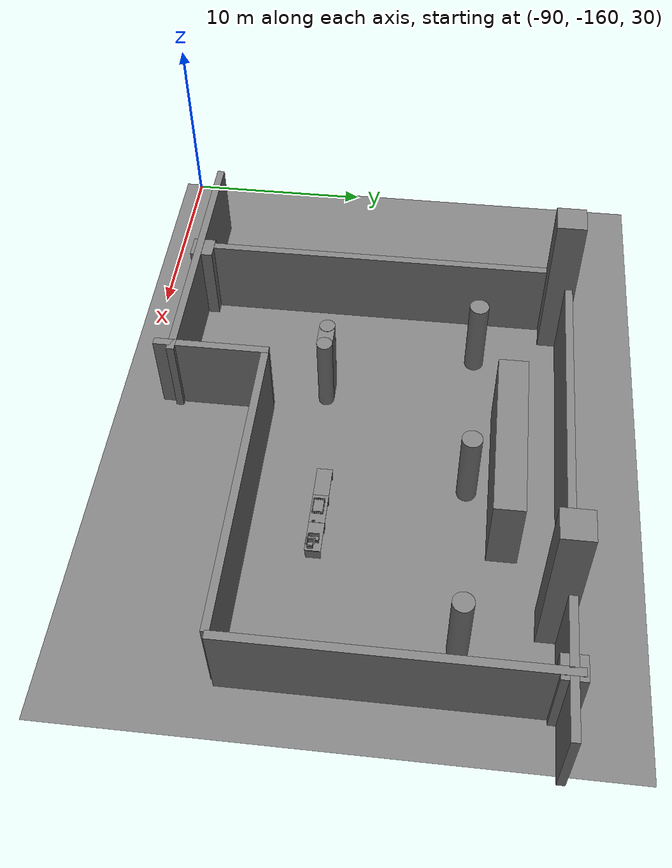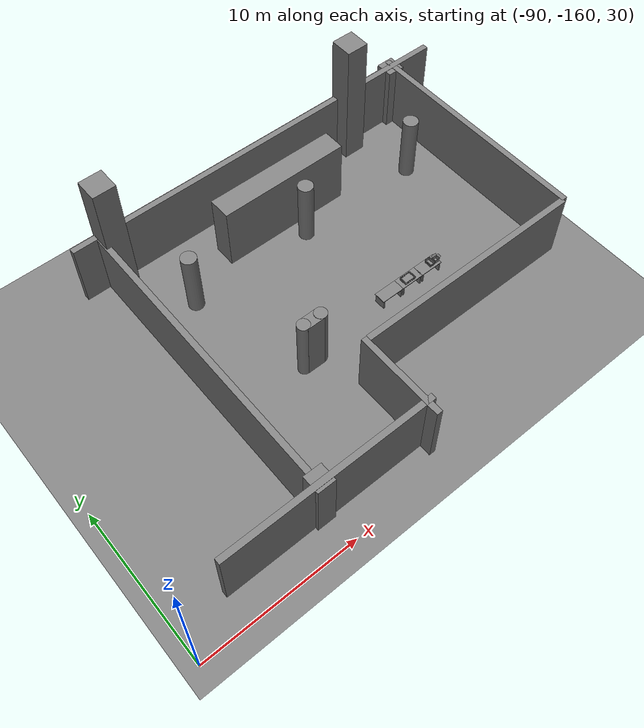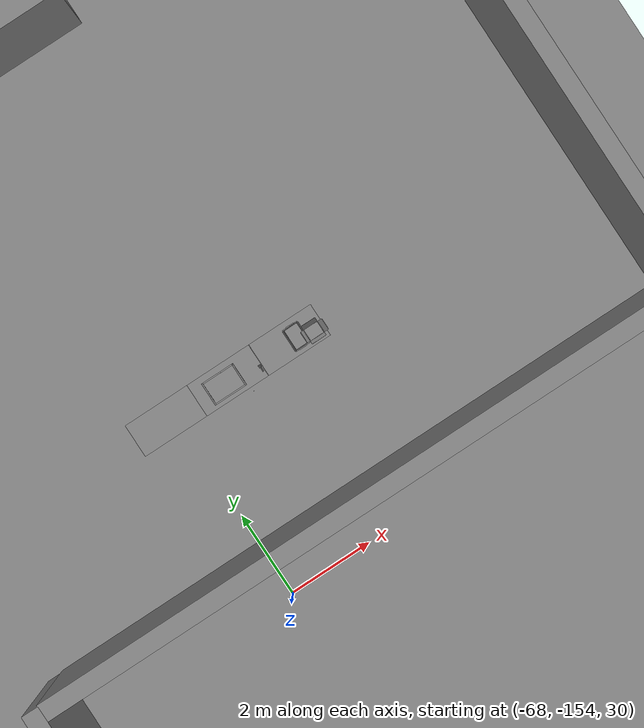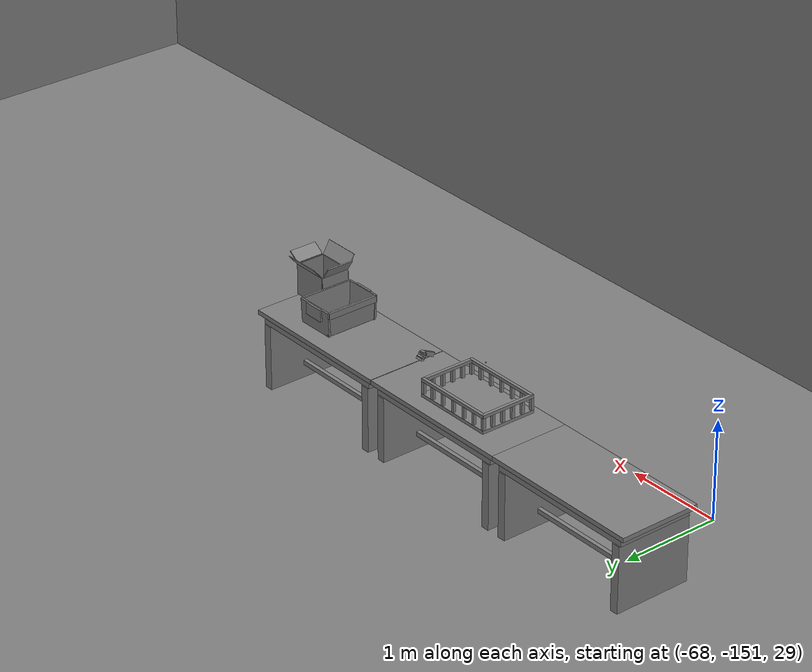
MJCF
<mujoco>
    <option gravity="0.000000000 0.000000000 -9.810000420" timestep="0.0049999999" integrator="implicitfast" density="1.225" viscosity="1.8000001e-05" noslip_iterations="10" iterations="100" sdf_iterations="50">
        <flag multiccd="disable"/>
    </option>
    <size memory="1000M"/>
    <compiler coordinate="local"/>
    <worldbody>
        <light cutoff="30" pos="0 1 1" dir="0 -1 -2"/>
        <light cutoff="30" pos="0 -1 1" dir="0 1 -2"/>
        <body pos="-64.866622925 -149.383972168 30.183746338" euler="89.999992371 89.999946594 0.000000000" name="openloong_gripper_2f85_fix_base_usda_bluebox_01">
            <geom contype="1" conaffinity="1" density="1000" type="box" material="" rgba="0.500000000 0.500000000 0.500000000 1.000000000" solimp="0.899999976 0.949999988 0.001000000" friction="1.000000000 0.005000000 0.000100000" solref="0.020000000 1.000000000" margin="0" condim="3" group="0" pos="0.276596069 0.187225342 0.000061035" quat="0.707107008 0.000077501 0.707106471 0.000077456" size="0.100000001 0.057999998 0.010000000" name="openloong_gripper_2f85_fix_base_usda_geom_D5434715_5A5E_47C1_A1DE_2E0566A2198A"/>
            <geom contype="1" conaffinity="1" density="1000" type="box" material="" rgba="0.500000000 0.500000000 0.500000000 1.000000000" solimp="0.899999976 0.949999988 0.001000000" friction="1.000000000 0.005000000 0.000100000" solref="0.020000000 1.000000000" margin="0" condim="3" group="0" pos="0.000000000 0.002883911 0.000000000" quat="1.000000000 0.000000000 0.000000000 0.000000000" size="0.254000008 0.003000000 0.172000006" name="openloong_gripper_2f85_fix_base_usda_geom_3ACA2CCC_727F_4727_9D03_11D9C6438689"/>
            <geom contype="1" conaffinity="1" density="1000" type="box" material="" rgba="0.500000000 0.500000000 0.500000000 1.000000000" solimp="0.899999976 0.949999988 0.001000000" friction="1.000000000 0.005000000 0.000100000" solref="0.020000000 1.000000000" margin="0" condim="3" group="0" pos="0.000015259 0.124874115 0.173477173" quat="0.999796450 0.020176515 -0.000000015 0.000000030" size="0.259999990 0.119999997 0.007000000" name="openloong_gripper_2f85_fix_base_usda_geom_76918312_AD96_4AD7_8A4C_1062A8C7E4C5"/>
            <geom contype="1" conaffinity="1" density="1000" type="box" material="" rgba="0.500000000 0.500000000 0.500000000 1.000000000" solimp="0.899999976 0.949999988 0.001000000" friction="1.000000000 0.005000000 0.000100000" solref="0.020000000 1.000000000" margin="0" condim="3" group="0" pos="0.000015259 0.124874115 -0.173477173" quat="0.999796450 -0.020176545 -0.000000015 0.000000000" size="0.259999990 0.119999997 0.007000000" name="openloong_gripper_2f85_fix_base_usda_geom_BC7A05B4_BC9C_46FB_A1D4_BF625EC5181F"/>
            <geom contype="1" conaffinity="1" density="1000" type="box" material="" rgba="0.500000000 0.500000000 0.500000000 1.000000000" solimp="0.899999976 0.949999988 0.001000000" friction="1.000000000 0.005000000 0.000100000" solref="0.020000000 1.000000000" margin="0" condim="3" group="0" pos="0.000015259 0.214012146 0.188980103" quat="0.999913096 0.013176724 0.000000015 0.000000000" size="0.259999990 0.029999999 0.012500000" name="openloong_gripper_2f85_fix_base_usda_geom_1C1ED57B_DFD9_4508_ADFC_500FAAEC28B8"/>
            <geom contype="1" conaffinity="1" density="1000" type="box" material="" rgba="0.500000000 0.500000000 0.500000000 1.000000000" solimp="0.899999976 0.949999988 0.001000000" friction="1.000000000 0.005000000 0.000100000" solref="0.020000000 1.000000000" margin="0" condim="3" group="0" pos="-0.258346558 0.125289917 0.001876831" quat="0.702796996 -0.020792052 0.710783184 0.020769238" size="0.189999998 0.119999997 0.009000000" name="openloong_gripper_2f85_fix_base_usda_geom_24953C6F_FB68_4174_89EB_A6DC7A77678E"/>
            <geom contype="1" conaffinity="1" density="1000" type="box" material="" rgba="0.500000000 0.500000000 0.500000000 1.000000000" solimp="0.899999976 0.949999988 0.001000000" friction="1.000000000 0.005000000 0.000100000" solref="0.020000000 1.000000000" margin="0" condim="3" group="0" pos="0.000015259 0.214012146 -0.188980103" quat="0.999913096 -0.013176769 0.000000030 0.000000015" size="0.259999990 0.029999999 0.012500000" name="openloong_gripper_2f85_fix_base_usda_geom_0AF4C45D_583E_4387_BB45_F0689A8F807F"/>
            <geom contype="1" conaffinity="1" density="1000" type="box" material="" rgba="0.500000000 0.500000000 0.500000000 1.000000000" solimp="0.899999976 0.949999988 0.001000000" friction="1.000000000 0.005000000 0.000100000" solref="0.020000000 1.000000000" margin="0" condim="3" group="0" pos="-0.276596069 0.187225342 0.000061035" quat="0.707106650 0.000077441 0.707106709 0.000077456" size="0.100000001 0.057999998 0.010000000" name="openloong_gripper_2f85_fix_base_usda_geom_BE101C34_4D89_4241_8225_3BF97F8E1BEF"/>
            <geom contype="1" conaffinity="1" density="1000" type="box" material="" rgba="0.500000000 0.500000000 0.500000000 1.000000000" solimp="0.899999976 0.949999988 0.001000000" friction="1.000000000 0.005000000 0.000100000" solref="0.020000000 1.000000000" margin="0" condim="3" group="0" pos="0.258346558 0.125289917 0.001876831" quat="0.702851534 0.018856451 0.710823834 -0.019329429" size="0.189999998 0.119999997 0.009000000" name="openloong_gripper_2f85_fix_base_usda_geom_211B3286_3706_4405_8F14_8111054CD48E"/>
            <freejoint name="openloong_gripper_2f85_fix_base_usda_bluebox_01_joint"/>
            <site size="0.005000000 0.005000000 0.005000000" rgba="0.500000000 0.500000000 0.500000000 1.000000000" pos="0.000000000 0.000000000 0.000000000" quat="0.999961913 0.008726534 0.000000000 0.000000000" group="0" type="sphere" name="openloong_gripper_2f85_fix_base_usda_bluebox_01site"/>
        </body>
        <body pos="-64.496299744 -149.491867065 30.235729218" euler="0.000000000 0.000000000 89.999946594" name="openloong_gripper_2f85_fix_base_usda_cardboardbox_01">
            <geom contype="1" conaffinity="1" density="1000" type="box" material="" rgba="0.500000000 0.500000000 0.500000000 1.000000000" solimp="0.899999976 0.949999988 0.001000000" friction="1.000000000 0.005000000 0.000100000" solref="0.020000000 1.000000000" margin="0" condim="3" group="0" pos="-0.003166199 -0.004086494 0.005052090" quat="1.000000000 0.000000000 0.000000000 0.000000000" size="0.142499998 0.177500010 0.005000000" name="openloong_gripper_2f85_fix_base_usda_geom_B44DAD39_6C0C_40F7_95D0_96B8D968EC46"/>
            <geom contype="1" conaffinity="1" density="1000" type="box" material="" rgba="0.500000000 0.500000000 0.500000000 1.000000000" solimp="0.899999976 0.949999988 0.001000000" friction="1.000000000 0.005000000 0.000100000" solref="0.020000000 1.000000000" margin="0" condim="3" group="0" pos="-0.003166199 0.170316696 0.150570869" quat="1.000000000 0.000000000 0.000000000 0.000000000" size="0.142499998 0.005000000 0.149999991" name="openloong_gripper_2f85_fix_base_usda_geom_6E947CED_E229_472D_89D0_FF55FD01CF35"/>
            <geom contype="1" conaffinity="1" density="1000" type="box" material="" rgba="0.500000000 0.500000000 0.500000000 1.000000000" solimp="0.899999976 0.949999988 0.001000000" friction="1.000000000 0.005000000 0.000100000" solref="0.020000000 1.000000000" margin="0" condim="3" group="0" pos="-0.147399902 -0.005307198 0.150570869" quat="1.000000000 0.000000000 0.000000000 0.000000000" size="0.005000000 0.177500010 0.149999991" name="openloong_gripper_2f85_fix_base_usda_geom_D614E9FC_8D8B_487E_AD4C_C2458834B03E"/>
            <geom contype="1" conaffinity="1" density="1000" type="box" material="" rgba="0.500000000 0.500000000 0.500000000 1.000000000" solimp="0.899999976 0.949999988 0.001000000" friction="1.000000000 0.005000000 0.000100000" solref="0.020000000 1.000000000" margin="0" condim="3" group="0" pos="0.140275955 -0.005307198 0.150570869" quat="1.000000000 0.000000000 0.000000000 0.000000000" size="0.005000000 0.177500010 0.149999991" name="openloong_gripper_2f85_fix_base_usda_geom_739D1120_6546_4825_BDB5_0C24B3DB9CFC"/>
            <geom contype="1" conaffinity="1" density="1000" type="box" material="" rgba="0.500000000 0.500000000 0.500000000 1.000000000" solimp="0.899999976 0.949999988 0.001000000" friction="1.000000000 0.005000000 0.000100000" solref="0.020000000 1.000000000" margin="0" condim="3" group="0" pos="-0.003166199 -0.181550980 0.150570869" quat="1.000000000 0.000000000 0.000000000 0.000000000" size="0.142499998 0.005000000 0.149999991" name="openloong_gripper_2f85_fix_base_usda_geom_42D87ECF_17CD_4222_B908_3C7A77C74255"/>
            <freejoint name="openloong_gripper_2f85_fix_base_usda_cardboardbox_01_joint"/>
            <site size="0.005000000 0.005000000 0.005000000" rgba="0.500000000 0.500000000 0.500000000 1.000000000" pos="0.000000000 0.000000000 0.000000000" quat="0.999961913 0.008726535 0.000000000 0.000000000" group="0" type="sphere" name="openloong_gripper_2f85_fix_base_usda_site_65C8A1B0_43CB_49BC_AC7C_8A8E9BF77731"/>
            <body pos="0.139160156 -0.004048347 0.301930904" euler="-179.999954224 49.383502960 179.999954224" name="openloong_gripper_2f85_fix_base_usda_A1_006">
                <geom contype="1" conaffinity="1" density="1000" type="box" material="" rgba="0.500000000 0.500000000 0.500000000 1.000000000" solimp="0.899999976 0.949999988 0.001000000" friction="1.000000000 0.005000000 0.000100000" solref="0.020000000 1.000000000" margin="0" condim="3" group="0" pos="-0.071587563 0.000009537 0.001745224" quat="0.999999881 0.000000000 0.000000000 0.000000000" size="0.071249999 0.179999992 0.002500000" name="openloong_gripper_2f85_fix_base_usda_geom_EDC64996_2C09_4D2D_912E_A83D7FB68125"/>
                <joint armature="0" stiffness="0.07" damping="0.0099999998" axis="0.000000 1.000000 0.000000" type="hinge" name="openloong_gripper_2f85_fix_base_usda_A1_006"/>
            </body>
            <body pos="-0.145902634 -0.004086494 0.301938057" euler="-180.000000000 -60.000011444 -180.000000000" name="openloong_gripper_2f85_fix_base_usda_A2_006">
                <geom contype="1" conaffinity="1" density="1000" type="box" material="" rgba="0.500000000 0.500000000 0.500000000 1.000000000" solimp="0.899999976 0.949999988 0.001000000" friction="1.000000000 0.005000000 0.000100000" solref="0.020000000 1.000000000" margin="0" condim="3" group="0" pos="0.071268082 0.000009537 0.002717972" quat="0.000002921 0.000000000 -0.000000030 0.999999881" size="0.071249999 0.179999992 0.002500000" name="openloong_gripper_2f85_fix_base_usda_geom_D4F1DAFC_E872_460A_8225_3ABE068935C9"/>
                <joint armature="0" stiffness="0.07" damping="0.0099999998" axis="0.000000 1.000000 0.000000" type="hinge" name="openloong_gripper_2f85_fix_base_usda_A2_006"/>
            </body>
            <body pos="-0.003385544 0.175991058 0.301930904" euler="-125.858116150 -0.000004561 0.000002331" name="openloong_gripper_2f85_fix_base_usda_B2_006">
                <geom contype="1" conaffinity="1" density="1000" type="box" material="" rgba="0.500000000 0.500000000 0.500000000 1.000000000" solimp="0.899999976 0.949999988 0.001000000" friction="1.000000000 0.005000000 0.000100000" solref="0.020000000 1.000000000" margin="0" condim="3" group="0" pos="0.000009537 -0.070939064 -0.002470016" quat="0.999614120 0.027776197 -0.000000015 0.000000030" size="0.137500003 0.064999998 0.005000000" name="openloong_gripper_2f85_fix_base_usda_geom_712FE934_5349_4AB8_93CA_6A369C113933"/>
                <joint armature="0" stiffness="0.07" damping="0.0099999998" axis="1.000000 0.000000 0.000000" type="hinge" name="openloong_gripper_2f85_fix_base_usda_B2_006"/>
            </body>
            <body pos="-0.003385544 -0.184140205 0.301938057" euler="147.805557251 0.000000000 0.000000000" name="openloong_gripper_2f85_fix_base_usda_B1_006">
                <geom contype="1" conaffinity="1" density="1000" type="box" material="" rgba="0.500000000 0.500000000 0.500000000 1.000000000" solimp="0.899999976 0.949999988 0.001000000" friction="1.000000000 0.005000000 0.000100000" solref="0.020000000 1.000000000" margin="0" condim="3" group="0" pos="-0.000028610 0.070202351 -0.002703667" quat="0.999614179 -0.027776167 0.000000000 0.000000000" size="0.137500003 0.064999998 0.005000000" name="openloong_gripper_2f85_fix_base_usda_geom_819EF08A_ADB2_41A4_A0BA_F40F4E119259"/>
                <joint armature="0" stiffness="0.07" damping="0.0099999998" axis="1.000000 0.000000 0.000000" type="hinge" name="openloong_gripper_2f85_fix_base_usda_B1_006"/>
            </body>
        </body>
        <body pos="-65.882858276 -149.481979370 30.229999542" euler="-64.487716675 0.000000000 0.000000000" name="openloong_gripper_2f85_fix_base_usda_Barcode">
            <geom contype="1" conaffinity="1" density="1000" type="box" material="" rgba="0.500000000 0.500000000 0.500000000 1.000000000" solimp="0.899999976 0.949999988 0.001000000" friction="1.000000000 0.005000000 0.000100000" solref="0.020000000 1.000000000" margin="0" condim="3" group="0" pos="0.000000000 0.013038635 0.001419067" quat="0.000000000 0.000000000 0.000000000 1.000000119" size="0.034000002 0.010000000 0.017999999" name="openloong_gripper_2f85_fix_base_usda_geom_F3DEDB3B_51A5_4EF6_98C9_FDF411B49DFE"/>
            <geom contype="1" conaffinity="1" density="1000" type="box" material="" rgba="0.500000000 0.500000000 0.500000000 1.000000000" solimp="0.899999976 0.949999988 0.001000000" friction="1.000000000 0.005000000 0.000100000" solref="0.020000000 1.000000000" margin="0" condim="3" group="0" pos="0.000000000 -0.035301208 -0.007095337" quat="0.000000000 0.000000000 -0.043619365 0.999048233" size="0.028999999 0.010000000 0.020000000" name="openloong_gripper_2f85_fix_base_usda_geom_417673E5_CA93_4C61_B02D_5A5DFE67DCE7"/>
            <geom contype="1" conaffinity="1" density="1000" type="box" material="" rgba="0.500000000 0.500000000 0.500000000 1.000000000" solimp="0.899999976 0.949999988 0.001000000" friction="1.000000000 0.005000000 0.000100000" solref="0.020000000 1.000000000" margin="0" condim="3" group="0" pos="0.000000000 -0.043411255 -0.011749268" quat="0.922262907 0.386563420 0.000000000 0.000000000" size="0.026000001 0.010000000 0.020000000" name="openloong_gripper_2f85_fix_base_usda_geom_D7733C37_C567_4E4F_992B_CFEF8791CF65"/>
            <geom contype="1" conaffinity="1" density="1000" type="box" material="" rgba="0.500000000 0.500000000 0.500000000 1.000000000" solimp="0.899999976 0.949999988 0.001000000" friction="1.000000000 0.005000000 0.000100000" solref="0.020000000 1.000000000" margin="0" condim="3" group="0" pos="0.000000000 -0.016967773 -0.031860352" quat="0.000000000 0.000000000 0.000000000 1.000000119" size="0.008000000 0.010000000 0.013000000" name="openloong_gripper_2f85_fix_base_usda_geom_196034FE_498F_45B1_B436_734D3F22E061"/>
            <geom contype="1" conaffinity="1" density="1000" type="box" material="" rgba="0.500000000 0.500000000 0.500000000 1.000000000" solimp="0.899999976 0.949999988 0.001000000" friction="1.000000000 0.005000000 0.000100000" solref="0.020000000 1.000000000" margin="0" condim="3" group="0" pos="0.000000000 -0.001869202 0.000312805" quat="0.953716993 0.300705761 0.000000000 0.000000000" size="0.032000002 0.010000000 0.018999999" name="openloong_gripper_2f85_fix_base_usda_geom_B2A36293_44A5_42BE_BC38_63E044A2AEDB"/>
            <geom contype="1" conaffinity="1" density="1000" type="box" material="" rgba="0.500000000 0.500000000 0.500000000 1.000000000" solimp="0.899999976 0.949999988 0.001000000" friction="1.000000000 0.005000000 0.000100000" solref="0.020000000 1.000000000" margin="0" condim="3" group="0" pos="0.000000000 -0.019531250 -0.003173828" quat="0.953716993 0.300705761 0.000000000 0.000000000" size="0.030999999 0.010000000 0.020000000" name="openloong_gripper_2f85_fix_base_usda_geom_B4A78D2B_BE7B_4CB2_9CF5_6D9934D6CDAA"/>
            <geom contype="1" conaffinity="1" density="1000" type="box" material="" rgba="0.500000000 0.500000000 0.500000000 1.000000000" solimp="0.899999976 0.949999988 0.001000000" friction="1.000000000 0.005000000 0.000100000" solref="0.020000000 1.000000000" margin="0" condim="3" group="0" pos="0.000000000 -0.035301208 -0.007095337" quat="0.953716993 0.300705761 0.000000000 0.000000000" size="0.028999999 0.010000000 0.020000000" name="openloong_gripper_2f85_fix_base_usda_geom_D53C56F4_57BE_477B_8F3B_0B56EE7EE6DE"/>
            <geom contype="1" conaffinity="1" density="1000" type="box" material="" rgba="0.500000000 0.500000000 0.500000000 1.000000000" solimp="0.899999976 0.949999988 0.001000000" friction="1.000000000 0.005000000 0.000100000" solref="0.020000000 1.000000000" margin="0" condim="3" group="0" pos="0.000000000 -0.042617798 -0.071121216" quat="0.000000000 0.000000000 0.000000000 1.000000119" size="0.013000000 0.021000000 0.059999999" name="openloong_gripper_2f85_fix_base_usda_geom_3F2B36CF_B87E_4872_8615_1669CACEF358"/>
            <freejoint name="openloong_gripper_2f85_fix_base_usda_Barcode_joint"/>
            <site size="0.005000000 0.005000000 0.005000000" rgba="0.500000000 0.500000000 0.500000000 1.000000000" pos="0.000000000 0.000000000 0.000000000" quat="1.000000000 0.000000000 0.000000000 0.000000000" group="0" type="sphere" name="openloong_gripper_2f85_fix_base_usda_Barcode_site"/>
        </body>
        <body pos="-66.745018005 -149.392349243 30.184000015" euler="0.000000000 0.000000000 89.999946594" name="[22332224849743]_Basket_01">
            <geom contype="1" conaffinity="1" density="1000" type="box" material="" rgba="0.500000000 0.500000000 0.500000000 1.000000000" solimp="0.899999976 0.949999988 0.001000000" friction="1.000000000 0.005000000 0.000100000" solref="0.020000000 1.000000000" margin="0" condim="3" group="0" pos="-0.052425385 0.389207840 0.089787483" quat="0.707107008 0.000000000 0.000000000 0.707106411" size="0.014249999 0.014249999 0.059999999" name="[22332224849743]_geom_4D00FA70_9CA9_4D85_B863_1DDD1626F1A2"/>
            <geom contype="1" conaffinity="1" density="1000" type="box" material="" rgba="0.500000000 0.500000000 0.500000000 1.000000000" solimp="0.899999976 0.949999988 0.001000000" friction="1.000000000 0.005000000 0.000100000" solref="0.020000000 1.000000000" margin="0" condim="3" group="0" pos="0.264015198 -0.133043289 0.089787483" quat="0.707107008 0.000000000 0.000000000 0.707106411" size="0.014249999 0.014249999 0.059999999" name="[22332224849743]_geom_1C347595_AC98_4217_AA9C_E52B10517798"/>
            <geom contype="1" conaffinity="1" density="1000" type="box" material="" rgba="0.500000000 0.500000000 0.500000000 1.000000000" solimp="0.899999976 0.949999988 0.001000000" friction="1.000000000 0.005000000 0.000100000" solref="0.020000000 1.000000000" margin="0" condim="3" group="0" pos="-0.264015198 -0.265548706 0.089793205" quat="0.707107008 0.000000000 0.000000000 0.707106411" size="0.014249999 0.014249999 0.059999999" name="[22332224849743]_geom_866EFD6C_D9A2_48FA_84A1_082AFE44ECAC"/>
            <geom contype="1" conaffinity="1" density="1000" type="box" material="" rgba="0.500000000 0.500000000 0.500000000 1.000000000" solimp="0.899999976 0.949999988 0.001000000" friction="1.000000000 0.005000000 0.000100000" solref="0.020000000 1.000000000" margin="0" condim="3" group="0" pos="-0.160263062 -0.389322281 0.089793205" quat="0.707107008 0.000000000 0.000000000 0.707106411" size="0.014249999 0.014249999 0.059999999" name="[22332224849743]_geom_8DAABC7D_9F38_42B0_82D5_44C35B48F1FD"/>
            <geom contype="1" conaffinity="1" density="1000" type="box" material="" rgba="0.500000000 0.500000000 0.500000000 1.000000000" solimp="0.899999976 0.949999988 0.001000000" friction="1.000000000 0.005000000 0.000100000" solref="0.020000000 1.000000000" margin="0" condim="3" group="0" pos="0.162265778 -0.389322281 0.089787483" quat="0.707107008 0.000000000 0.000000000 0.707106411" size="0.014249999 0.014249999 0.059999999" name="[22332224849743]_geom_25C38F4A_EA40_41BD_9CC1_691AB3F7F869"/>
            <geom contype="1" conaffinity="1" density="1000" type="box" material="" rgba="0.500000000 0.500000000 0.500000000 1.000000000" solimp="0.899999976 0.949999988 0.001000000" friction="1.000000000 0.005000000 0.000100000" solref="0.020000000 1.000000000" margin="0" condim="3" group="0" pos="0.264015198 0.389207840 0.089787483" quat="0.707107008 0.000000000 0.000000000 0.707106411" size="0.014249999 0.014249999 0.059999999" name="[22332224849743]_geom_9190BA2B_3D59_426E_85CD_A57DA0BD8315"/>
            <geom contype="1" conaffinity="1" density="1000" type="box" material="" rgba="0.500000000 0.500000000 0.500000000 1.000000000" solimp="0.899999976 0.949999988 0.001000000" friction="1.000000000 0.005000000 0.000100000" solref="0.020000000 1.000000000" margin="0" condim="3" group="0" pos="-0.264015198 -0.133043289 0.089793205" quat="0.707107008 0.000000000 0.000000000 0.707106411" size="0.014249999 0.014249999 0.059999999" name="[22332224849743]_geom_19FFE24E_A36F_4A4A_9874_7CCB58CFF2D8"/>
            <geom contype="1" conaffinity="1" density="1000" type="box" material="" rgba="0.500000000 0.500000000 0.500000000 1.000000000" solimp="0.899999976 0.949999988 0.001000000" friction="1.000000000 0.005000000 0.000100000" solref="0.020000000 1.000000000" margin="0" condim="3" group="0" pos="-0.264026642 0.269256592 0.089793205" quat="0.707107008 0.000000000 0.000000000 0.707106411" size="0.014249999 0.014249999 0.059999999" name="[22332224849743]_geom_2A22EDC7_1335_47FB_809B_CEF255740682"/>
            <geom contype="1" conaffinity="1" density="1000" type="box" material="" rgba="0.500000000 0.500000000 0.500000000 1.000000000" solimp="0.899999976 0.949999988 0.001000000" friction="1.000000000 0.005000000 0.000100000" solref="0.020000000 1.000000000" margin="0" condim="3" group="0" pos="0.054462433 0.389207840 0.089787483" quat="0.707107008 0.000000000 0.000000000 0.707106411" size="0.014249999 0.014249999 0.059999999" name="[22332224849743]_geom_9C6A9965_EB87_4C17_A683_546330AA5F60"/>
            <geom contype="1" conaffinity="1" density="1000" type="box" material="" rgba="0.500000000 0.500000000 0.500000000 1.000000000" solimp="0.899999976 0.949999988 0.001000000" friction="1.000000000 0.005000000 0.000100000" solref="0.020000000 1.000000000" margin="0" condim="3" group="0" pos="0.054462433 -0.389322281 0.089787483" quat="0.707107008 0.000000000 0.000000000 0.707106411" size="0.014249999 0.014249999 0.059999999" name="[22332224849743]_geom_4CC40CD3_85E6_4E9F_A5A7_2650C260DDD3"/>
            <geom contype="1" conaffinity="1" density="1000" type="box" material="" rgba="0.500000000 0.500000000 0.500000000 1.000000000" solimp="0.899999976 0.949999988 0.001000000" friction="1.000000000 0.005000000 0.000100000" solref="0.020000000 1.000000000" margin="0" condim="3" group="0" pos="0.264015198 0.269256592 0.089793205" quat="0.707107008 0.000000000 0.000000000 0.707106411" size="0.014249999 0.014249999 0.059999999" name="[22332224849743]_geom_2AB48214_AC16_4B0B_9256_A36B31557512"/>
            <geom contype="1" conaffinity="1" density="1000" type="box" material="" rgba="0.500000000 0.500000000 0.500000000 1.000000000" solimp="0.899999976 0.949999988 0.001000000" friction="1.000000000 0.005000000 0.000100000" solref="0.020000000 1.000000000" margin="0" condim="3" group="0" pos="0.264015198 -0.389322281 0.089787483" quat="0.707107008 0.000000000 0.000000000 0.707106411" size="0.014249999 0.014249999 0.059999999" name="[22332224849743]_geom_FBF63D88_6A2A_4DA9_A803_4A26CB3D75BB"/>
            <geom contype="1" conaffinity="1" density="1000" type="box" material="" rgba="0.500000000 0.500000000 0.500000000 1.000000000" solimp="0.899999976 0.949999988 0.001000000" friction="1.000000000 0.005000000 0.000100000" solref="0.020000000 1.000000000" margin="0" condim="3" group="0" pos="0.000000000 0.000000000 0.015998840" quat="0.707107008 0.000000000 0.000000000 0.707106411" size="0.403499991 0.279000014 0.015750000" name="[22332224849743]_geom_2BDE5C4D_E05B_4BE5_8C65_72CDD6A06899"/>
            <geom contype="1" conaffinity="1" density="1000" type="box" material="" rgba="0.500000000 0.500000000 0.500000000 1.000000000" solimp="0.899999976 0.949999988 0.001000000" friction="1.000000000 0.005000000 0.000100000" solref="0.020000000 1.000000000" margin="0" condim="3" group="0" pos="0.000000000 -0.389476776 0.163619041" quat="0.707107008 0.000000000 0.000000000 0.707106411" size="0.015000000 0.277500004 0.015750000" name="[22332224849743]_geom_93E83452_A7F2_4895_A1E0_71FE41FA1E64"/>
            <geom contype="1" conaffinity="1" density="1000" type="box" material="" rgba="0.500000000 0.500000000 0.500000000 1.000000000" solimp="0.899999976 0.949999988 0.001000000" friction="1.000000000 0.005000000 0.000100000" solref="0.020000000 1.000000000" margin="0" condim="3" group="0" pos="0.162265778 0.389207840 0.089787483" quat="0.707107008 0.000000000 0.000000000 0.707106411" size="0.014249999 0.014249999 0.059999999" name="[22332224849743]_geom_4ABEB012_FBDE_4AF5_8F57_8144791BD301"/>
            <geom contype="1" conaffinity="1" density="1000" type="box" material="" rgba="0.500000000 0.500000000 0.500000000 1.000000000" solimp="0.899999976 0.949999988 0.001000000" friction="1.000000000 0.005000000 0.000100000" solref="0.020000000 1.000000000" margin="0" condim="3" group="0" pos="0.000000000 0.389471054 0.163619041" quat="0.707107008 0.000000000 0.000000000 0.707106411" size="0.015000000 0.277500004 0.015750000" name="[22332224849743]_geom_2F5F2999_3568_4F38_8EC7_18AA9D00BCE7"/>
            <geom contype="1" conaffinity="1" density="1000" type="box" material="" rgba="0.500000000 0.500000000 0.500000000 1.000000000" solimp="0.899999976 0.949999988 0.001000000" friction="1.000000000 0.005000000 0.000100000" solref="0.020000000 1.000000000" margin="0" condim="3" group="0" pos="-0.263511658 0.000000000 0.163619041" quat="0.707107008 0.000000000 0.000000000 0.707106411" size="0.403499991 0.015000000 0.015750000" name="[22332224849743]_geom_AED8F819_C9B5_42BF_AD13_EDE4227DCF79"/>
            <geom contype="1" conaffinity="1" density="1000" type="box" material="" rgba="0.500000000 0.500000000 0.500000000 1.000000000" solimp="0.899999976 0.949999988 0.001000000" friction="1.000000000 0.005000000 0.000100000" solref="0.020000000 1.000000000" margin="0" condim="3" group="0" pos="-0.264015198 0.141334534 0.089793205" quat="0.707107008 0.000000000 0.000000000 0.707106411" size="0.014249999 0.014249999 0.059999999" name="[22332224849743]_geom_9DE369C7_92AB_4988_A385_CB27A54391F3"/>
            <geom contype="1" conaffinity="1" density="1000" type="box" material="" rgba="0.500000000 0.500000000 0.500000000 1.000000000" solimp="0.899999976 0.949999988 0.001000000" friction="1.000000000 0.005000000 0.000100000" solref="0.020000000 1.000000000" margin="0" condim="3" group="0" pos="0.264015198 -0.265548706 0.089787483" quat="0.707107008 0.000000000 0.000000000 0.707106411" size="0.014249999 0.014249999 0.059999999" name="[22332224849743]_geom_6D285B97_4C6A_418C_9D0B_13A42A5AFE04"/>
            <geom contype="1" conaffinity="1" density="1000" type="box" material="" rgba="0.500000000 0.500000000 0.500000000 1.000000000" solimp="0.899999976 0.949999988 0.001000000" friction="1.000000000 0.005000000 0.000100000" solref="0.020000000 1.000000000" margin="0" condim="3" group="0" pos="-0.160263062 0.389207840 0.089787483" quat="0.707107008 0.000000000 0.000000000 0.707106411" size="0.014249999 0.014249999 0.059999999" name="[22332224849743]_geom_4DB93575_263B_47BB_AE94_C9F451199DF0"/>
            <geom contype="1" conaffinity="1" density="1000" type="box" material="" rgba="0.500000000 0.500000000 0.500000000 1.000000000" solimp="0.899999976 0.949999988 0.001000000" friction="1.000000000 0.005000000 0.000100000" solref="0.020000000 1.000000000" margin="0" condim="3" group="0" pos="-0.052425385 -0.389322281 0.089787483" quat="0.707107008 0.000000000 0.000000000 0.707106411" size="0.014249999 0.014249999 0.059999999" name="[22332224849743]_geom_B0A7B492_44DA_4507_9F16_AF2CC55EC452"/>
            <geom contype="1" conaffinity="1" density="1000" type="box" material="" rgba="0.500000000 0.500000000 0.500000000 1.000000000" solimp="0.899999976 0.949999988 0.001000000" friction="1.000000000 0.005000000 0.000100000" solref="0.020000000 1.000000000" margin="0" condim="3" group="0" pos="-0.264026642 -0.389322281 0.089793205" quat="0.707107008 0.000000000 0.000000000 0.707106411" size="0.014249999 0.014249999 0.059999999" name="[22332224849743]_geom_28ED79FF_A2EB_4CFF_BD8D_6B08745ADC14"/>
            <geom contype="1" conaffinity="1" density="1000" type="box" material="" rgba="0.500000000 0.500000000 0.500000000 1.000000000" solimp="0.899999976 0.949999988 0.001000000" friction="1.000000000 0.005000000 0.000100000" solref="0.020000000 1.000000000" margin="0" condim="3" group="0" pos="0.264015198 0.141334534 0.089787483" quat="0.707107008 0.000000000 0.000000000 0.707106411" size="0.014249999 0.014249999 0.059999999" name="[22332224849743]_geom_D5AE5DAC_F4C3_46CD_83B2_4B7C8786E7CA"/>
            <geom contype="1" conaffinity="1" density="1000" type="box" material="" rgba="0.500000000 0.500000000 0.500000000 1.000000000" solimp="0.899999976 0.949999988 0.001000000" friction="1.000000000 0.005000000 0.000100000" solref="0.020000000 1.000000000" margin="0" condim="3" group="0" pos="-0.264015198 0.389207840 0.089793205" quat="0.707107008 0.000000000 0.000000000 0.707106411" size="0.014249999 0.014249999 0.059999999" name="[22332224849743]_geom_27B7E96E_90C1_496D_B516_133D85C05170"/>
            <geom contype="1" conaffinity="1" density="1000" type="box" material="" rgba="0.500000000 0.500000000 0.500000000 1.000000000" solimp="0.899999976 0.949999988 0.001000000" friction="1.000000000 0.005000000 0.000100000" solref="0.020000000 1.000000000" margin="0" condim="3" group="0" pos="0.264015198 0.004480362 0.089787483" quat="0.707107008 0.000000000 0.000000000 0.707106411" size="0.014249999 0.014249999 0.059999999" name="[22332224849743]_geom_D61C2C9B_31B8_4615_BAF4_BA107B5144F7"/>
            <geom contype="1" conaffinity="1" density="1000" type="box" material="" rgba="0.500000000 0.500000000 0.500000000 1.000000000" solimp="0.899999976 0.949999988 0.001000000" friction="1.000000000 0.005000000 0.000100000" solref="0.020000000 1.000000000" margin="0" condim="3" group="0" pos="0.263694763 -0.000011444 0.163619041" quat="0.707107008 0.000000000 0.000000000 0.707106411" size="0.403499991 0.015000000 0.015750000" name="[22332224849743]_geom_1C426D9D_FE9A_42AF_B4B1_EB5E3AE2D418"/>
            <geom contype="1" conaffinity="1" density="1000" type="box" material="" rgba="0.500000000 0.500000000 0.500000000 1.000000000" solimp="0.899999976 0.949999988 0.001000000" friction="1.000000000 0.005000000 0.000100000" solref="0.020000000 1.000000000" margin="0" condim="3" group="0" pos="-0.264015198 0.004480362 0.089793205" quat="0.707107008 0.000000000 0.000000000 0.707106411" size="0.014249999 0.014249999 0.059999999" name="[22332224849743]_geom_24F0CA44_419E_46ED_A237_F640B234F817"/>
            <freejoint name="[22332224849743]_joint_8F3A7249_25DB_4028_8556_42F0705C555A"/>
        </body>
        <body pos="0.000000000 0.000000000 0.000000000" euler="0.000000000 0.000000000 0.000000000" name="Static Objects_Static Objects">
            <geom contype="1" conaffinity="1" density="1000" type="box" material="" rgba="0.500000000 0.500000000 0.500000000 1.000000000" solimp="0.899999976 0.949999988 0.001000000" friction="1.000000000 0.005000000 0.000100000" solref="0.020000000 1.000000000" margin="0" condim="3" group="0" pos="-67.544113159 -149.365814209 29.727830887" quat="0.500000417 0.499999970 0.499999553 0.499999970" size="0.381000012 0.319999993 0.041000001" name="Static Objects_geom_11BDC53D_B049_4365_B9CA_DE264B641B8D"/>
            <geom contype="1" conaffinity="1" density="1000" type="box" material="" rgba="0.500000000 0.500000000 0.500000000 1.000000000" solimp="0.899999976 0.949999988 0.001000000" friction="1.000000000 0.005000000 0.000100000" solref="0.020000000 1.000000000" margin="0" condim="3" group="0" pos="-68.239501953 -149.365814209 30.086868286" quat="0.500000417 0.499999970 0.499999553 0.499999970" size="0.370999992 0.039500002 0.745000005" name="Static Objects_geom_815C2F2D_2638_4ABF_93C5_39D6FFDB9127"/>
            <geom contype="1" conaffinity="1" density="1000" type="box" material="" rgba="0.500000000 0.500000000 0.500000000 1.000000000" solimp="0.899999976 0.949999988 0.001000000" friction="1.000000000 0.005000000 0.000100000" solref="0.020000000 1.000000000" margin="0" condim="3" group="0" pos="-68.239501953 -149.365814209 30.147235870" quat="0.500000417 0.499999970 0.499999553 0.499999970" size="0.400000006 0.022000000 0.800000012" name="Static Objects_geom_E64CD098_4E3E_40E3_8686_36CF0442E696"/>
            <geom contype="1" conaffinity="1" density="1000" type="box" material="" rgba="0.500000000 0.500000000 0.500000000 1.000000000" solimp="0.899999976 0.949999988 0.001000000" friction="1.000000000 0.005000000 0.000100000" solref="0.020000000 1.000000000" margin="0" condim="3" group="0" pos="-68.934890747 -149.365814209 29.727830887" quat="0.500000417 0.499999970 0.499999553 0.499999970" size="0.381000012 0.319999993 0.041000001" name="Static Objects_geom_DD779C1B_6DD2_4EB0_855F_14ED8745353E"/>
            <geom contype="1" conaffinity="1" density="1000" type="box" material="" rgba="0.500000000 0.500000000 0.500000000 1.000000000" solimp="0.899999976 0.949999988 0.001000000" friction="1.000000000 0.005000000 0.000100000" solref="0.020000000 1.000000000" margin="0" condim="3" group="0" pos="-68.239501953 -149.365814209 29.561563492" quat="0.500000417 0.499999970 0.499999553 0.499999970" size="0.020000000 0.022000000 0.660000026" name="Static Objects_geom_37AA44FF_6846_4582_9914_E4CBF743F456"/>
            <geom contype="1" conaffinity="1" density="1000" type="box" material="" rgba="0.500000000 0.500000000 0.500000000 1.000000000" solimp="0.899999976 0.949999988 0.001000000" friction="1.000000000 0.005000000 0.000100000" solref="0.020000000 1.000000000" margin="0" condim="3" group="0" pos="-65.945671082 -149.365814209 29.727830887" quat="0.500000417 0.499999970 0.499999553 0.499999970" size="0.381000012 0.319999993 0.041000001" name="Static Objects_geom_341F907E_8DDF_4BC9_86E4_A68A6FAE7887"/>
            <geom contype="1" conaffinity="1" density="1000" type="box" material="" rgba="0.500000000 0.500000000 0.500000000 1.000000000" solimp="0.899999976 0.949999988 0.001000000" friction="1.000000000 0.005000000 0.000100000" solref="0.020000000 1.000000000" margin="0" condim="3" group="0" pos="-66.641059875 -149.365814209 30.086868286" quat="0.500000417 0.499999970 0.499999553 0.499999970" size="0.370999992 0.039500002 0.745000005" name="Static Objects_geom_FE380B97_AEAE_496F_8182_25A8D692C525"/>
            <geom contype="1" conaffinity="1" density="1000" type="box" material="" rgba="0.500000000 0.500000000 0.500000000 1.000000000" solimp="0.899999976 0.949999988 0.001000000" friction="1.000000000 0.005000000 0.000100000" solref="0.020000000 1.000000000" margin="0" condim="3" group="0" pos="-66.641059875 -149.365814209 30.147235870" quat="0.500000417 0.499999970 0.499999553 0.499999970" size="0.400000006 0.022000000 0.800000012" name="Static Objects_geom_33F85065_5A6E_40EA_BEC3_ED730CB13487"/>
            <geom contype="1" conaffinity="1" density="1000" type="box" material="" rgba="0.500000000 0.500000000 0.500000000 1.000000000" solimp="0.899999976 0.949999988 0.001000000" friction="1.000000000 0.005000000 0.000100000" solref="0.020000000 1.000000000" margin="0" condim="3" group="0" pos="-67.336448669 -149.365814209 29.727830887" quat="0.500000417 0.499999970 0.499999553 0.499999970" size="0.381000012 0.319999993 0.041000001" name="Static Objects_geom_65112D58_F589_4087_A771_D244B90DFB91"/>
            <geom contype="1" conaffinity="1" density="1000" type="box" material="" rgba="0.500000000 0.500000000 0.500000000 1.000000000" solimp="0.899999976 0.949999988 0.001000000" friction="1.000000000 0.005000000 0.000100000" solref="0.020000000 1.000000000" margin="0" condim="3" group="0" pos="-66.641059875 -149.365814209 29.561563492" quat="0.500000417 0.499999970 0.499999553 0.499999970" size="0.020000000 0.022000000 0.660000026" name="Static Objects_geom_3CAAF1DB_7F05_4F86_BBD6_F73DF7F91405"/>
            <geom contype="1" conaffinity="1" density="1000" type="box" material="" rgba="0.500000000 0.500000000 0.500000000 1.000000000" solimp="0.899999976 0.949999988 0.001000000" friction="1.000000000 0.005000000 0.000100000" solref="0.020000000 1.000000000" margin="0" condim="3" group="0" pos="-64.338577271 -149.365814209 29.727830887" quat="0.500000417 0.499999970 0.499999553 0.499999970" size="0.381000012 0.319999993 0.041000001" name="Static Objects_geom_078C92E7_9CCD_4D7F_806D_7D528491E7EF"/>
            <geom contype="1" conaffinity="1" density="1000" type="box" material="" rgba="0.500000000 0.500000000 0.500000000 1.000000000" solimp="0.899999976 0.949999988 0.001000000" friction="1.000000000 0.005000000 0.000100000" solref="0.020000000 1.000000000" margin="0" condim="3" group="0" pos="-65.033966064 -149.365814209 30.086868286" quat="0.500000417 0.499999970 0.499999553 0.499999970" size="0.370999992 0.039500002 0.745000005" name="Static Objects_geom_9F814E99_6886_4806_A08F_E83AB44DBE22"/>
            <geom contype="1" conaffinity="1" density="1000" type="box" material="" rgba="0.500000000 0.500000000 0.500000000 1.000000000" solimp="0.899999976 0.949999988 0.001000000" friction="1.000000000 0.005000000 0.000100000" solref="0.020000000 1.000000000" margin="0" condim="3" group="0" pos="-65.033966064 -149.365814209 30.147235870" quat="0.500000417 0.499999970 0.499999553 0.499999970" size="0.400000006 0.022000000 0.800000012" name="Static Objects_geom_66B3E1CD_D712_4B5B_BA36_83120D925E18"/>
            <geom contype="1" conaffinity="1" density="1000" type="box" material="" rgba="0.500000000 0.500000000 0.500000000 1.000000000" solimp="0.899999976 0.949999988 0.001000000" friction="1.000000000 0.005000000 0.000100000" solref="0.020000000 1.000000000" margin="0" condim="3" group="0" pos="-65.729354858 -149.365814209 29.727830887" quat="0.500000417 0.499999970 0.499999553 0.499999970" size="0.381000012 0.319999993 0.041000001" name="Static Objects_geom_D07F86EA_3990_4BCC_84E5_503C18B5C263"/>
            <geom contype="1" conaffinity="1" density="1000" type="box" material="" rgba="0.500000000 0.500000000 0.500000000 1.000000000" solimp="0.899999976 0.949999988 0.001000000" friction="1.000000000 0.005000000 0.000100000" solref="0.020000000 1.000000000" margin="0" condim="3" group="0" pos="-65.033966064 -149.365814209 29.561563492" quat="0.500000417 0.499999970 0.499999553 0.499999970" size="0.020000000 0.022000000 0.660000026" name="Static Objects_geom_9AA3895A_C8DA_4D55_9BBD_747633BC3B31"/>
            <geom contype="1" conaffinity="1" density="1000" type="box" material="" rgba="0.500000000 0.500000000 0.500000000 1.000000000" solimp="0.899999976 0.949999988 0.001000000" friction="1.000000000 0.005000000 0.000100000" solref="0.020000000 1.000000000" margin="0" condim="3" group="0" pos="-61.754566193 -137.853729248 33.906845093" quat="0.707107067 0.000000000 0.000000000 0.707106471" size="0.759999990 0.759999990 4.500000000" name="Static Objects_geom_25126F30_5AC0_4C12_A97B_13A14B02DB95"/>
            <geom contype="1" conaffinity="1" density="1000" type="box" material="" rgba="0.500000000 0.500000000 0.500000000 1.000000000" solimp="0.899999976 0.949999988 0.001000000" friction="1.000000000 0.005000000 0.000100000" solref="0.020000000 1.000000000" margin="0" condim="3" group="0" pos="-57.511135101 -144.927108765 31.707921982" quat="1.000000000 0.000000000 0.000000000 0.000000000" size="0.200000003 8.000000000 2.299999952" name="Static Objects_geom_325056E0_6928_41C9_A74F_7983D95271FA"/>
            <geom contype="1" conaffinity="1" density="1000" type="box" material="" rgba="0.500000000 0.500000000 0.500000000 1.000000000" solimp="0.899999976 0.949999988 0.001000000" friction="1.000000000 0.005000000 0.000100000" solref="0.020000000 1.000000000" margin="0" condim="3" group="0" pos="-80.517646790 -157.574050903 31.688196182" quat="0.707107067 0.000000000 0.000000000 0.707106471" size="0.600000024 0.600000024 2.299999952" name="Static Objects_geom_729E01F6_8C94_4192_81DF_86DDC39C8E44"/>
            <geom contype="1" conaffinity="1" density="1000" type="box" material="" rgba="0.500000000 0.500000000 0.500000000 1.000000000" solimp="0.899999976 0.949999988 0.001000000" friction="1.000000000 0.005000000 0.000100000" solref="0.020000000 1.000000000" margin="0" condim="3" group="0" pos="-80.711044312 -147.414932251 31.666158676" quat="1.000000000 0.000000000 0.000000000 0.000000000" size="0.200000003 10.000000000 2.299999952" name="Static Objects_geom_EFC1DBE5_DA89_48C1_B6B3_4547EA766F87"/>
            <geom contype="1" conaffinity="1" density="1000" type="box" material="" rgba="0.500000000 0.500000000 0.500000000 1.000000000" solimp="0.899999976 0.949999988 0.001000000" friction="1.000000000 0.005000000 0.000100000" solref="0.020000000 1.000000000" margin="0" condim="3" group="0" pos="-57.687217712 -137.434692383 31.688196182" quat="0.707107067 0.000000000 0.000000000 0.707106471" size="0.600000024 0.600000024 2.299999952" name="Static Objects_geom_30038EA8_ED22_4AE9_8CCD_04427A6EE393"/>
            <geom contype="1" conaffinity="1" density="1000" type="box" material="" rgba="0.500000000 0.500000000 0.500000000 1.000000000" solimp="0.899999976 0.949999988 0.001000000" friction="1.000000000 0.005000000 0.000100000" solref="0.020000000 1.000000000" margin="0" condim="3" group="0" pos="-69.537033081 -140.263229370 31.714921951" quat="0.707107067 0.000000000 0.000000000 0.707106471" size="0.759999990 4.500000000 2.299999952" name="Static Objects_geom_A1837BB3_295E_46FF_8E5F_7EA758DF4565"/>
            <geom contype="1" conaffinity="1" density="1000" type="box" material="" rgba="0.500000000 0.500000000 0.500000000 1.000000000" solimp="0.899999976 0.949999988 0.001000000" friction="1.000000000 0.005000000 0.000100000" solref="0.020000000 1.000000000" margin="0" condim="3" group="0" pos="-80.073638916 -137.853713989 33.906845093" quat="0.707107067 0.000000000 0.000000000 0.707106471" size="0.759999990 0.759999990 4.500000000" name="Static Objects_geom_F77907A3_945A_4487_93E6_F14468B23EE5"/>
            <geom contype="1" conaffinity="1" density="1000" type="box" material="" rgba="0.500000000 0.500000000 0.500000000 1.000000000" solimp="0.899999976 0.949999988 0.001000000" friction="1.000000000 0.005000000 0.000100000" solref="0.020000000 1.000000000" margin="0" condim="3" group="0" pos="-73.406707764 -155.734664917 31.707921982" quat="1.000000000 0.000000000 0.000000000 0.000000000" size="0.200000003 3.000000000 2.299999952" name="Static Objects_geom_7B532C18_CF3D_4BFD_B4CF_17E898950BD8"/>
            <geom contype="1" conaffinity="1" density="1000" type="box" material="" rgba="0.500000000 0.500000000 0.500000000 1.000000000" solimp="0.899999976 0.949999988 0.001000000" friction="1.000000000 0.005000000 0.000100000" solref="0.020000000 1.000000000" margin="0" condim="3" group="0" pos="-68.497543335 -137.448257446 31.707921982" quat="0.707107067 0.000000000 0.000000000 0.707106471" size="0.200000003 14.000000000 2.299999952" name="Static Objects_geom_25AC12FF_D08A_419D_AF10_EEC86CDE7FAF"/>
            <geom contype="1" conaffinity="1" density="1000" type="cylinder" material="" rgba="0.500000000 0.500000000 0.500000000 1.000000000" solimp="0.899999976 0.949999988 0.001000000" friction="1.000000000 0.005000000 0.000100000" solref="0.020000000 1.000000000" margin="0" condim="3" group="0" pos="-68.868522644 -142.134506226 31.711090088" quat="0.707107067 0.000000000 0.000000000 0.707106471" size="0.509999990 2.299999952 1.000000000" name="Static Objects_geom_8E2A6951_C643_4AE5_8F7B_E6A3EFDDBFEC"/>
            <geom contype="1" conaffinity="1" density="1000" type="plane" material="" rgba="0.500000000 0.500000000 0.500000000 1.000000000" solimp="0.899999976 0.949999988 0.001000000" friction="1.000000000 0.005000000 0.000100000" solref="0.020000000 1.000000000" margin="0" condim="3" group="0" pos="-72.873703003 -147.131927490 29.409669876" quat="1.000000000 0.000000000 0.000000000 0.000000000" size="18.000000000 14.000000000 1.000000000" name="Static Objects_geom_4D2AC97C_715A_4400_AFE8_A235EBAABE04"/>
            <geom contype="1" conaffinity="1" density="1000" type="box" material="" rgba="0.500000000 0.500000000 0.500000000 1.000000000" solimp="0.899999976 0.949999988 0.001000000" friction="1.000000000 0.005000000 0.000100000" solref="0.020000000 1.000000000" margin="0" condim="3" group="0" pos="-79.943580627 -157.782272339 31.707921982" quat="0.707107067 0.000000000 0.000000000 0.707106471" size="0.200000003 7.000000000 2.299999952" name="Static Objects_geom_253206D9_8B64_4D0F_867B_3D12A165708D"/>
            <geom contype="1" conaffinity="1" density="1000" type="box" material="" rgba="0.500000000 0.500000000 0.500000000 1.000000000" solimp="0.899999976 0.949999988 0.001000000" friction="1.000000000 0.005000000 0.000100000" solref="0.020000000 1.000000000" margin="0" condim="3" group="0" pos="-65.421028137 -152.903442383 31.707921982" quat="0.707107067 0.000000000 0.000000000 0.707106471" size="0.200000003 7.800000191 2.299999952" name="Static Objects_geom_217388C4_39FA_4ECA_9B20_9891411D28C1"/>
            <geom contype="1" conaffinity="1" density="1000" type="box" material="" rgba="0.500000000 0.500000000 0.500000000 1.000000000" solimp="0.899999976 0.949999988 0.001000000" friction="1.000000000 0.005000000 0.000100000" solref="0.020000000 1.000000000" margin="0" condim="3" group="0" pos="-74.776908875 -149.964416504 31.688196182" quat="1.000000000 0.000000000 0.000000000 0.000000000" size="0.600000024 0.409999996 2.299999952" name="Static Objects_geom_65293509_16A6_4289_9A6E_F877EE33C63D"/>
            <geom contype="1" conaffinity="1" density="1000" type="cylinder" material="" rgba="0.500000000 0.500000000 0.500000000 1.000000000" solimp="0.899999976 0.949999988 0.001000000" friction="1.000000000 0.005000000 0.000100000" solref="0.020000000 1.000000000" margin="0" condim="3" group="0" pos="-60.161884308 -142.134506226 31.711090088" quat="0.707107067 0.000000000 0.000000000 0.707106471" size="0.509999990 2.299999952 1.000000000" name="Static Objects_geom_0C07BBBA_9CA1_47AA_A42A_399F5C251C5D"/>
            <geom contype="1" conaffinity="1" density="1000" type="cylinder" material="" rgba="0.500000000 0.500000000 0.500000000 1.000000000" solimp="0.899999976 0.949999988 0.001000000" friction="1.000000000 0.005000000 0.000100000" solref="0.020000000 1.000000000" margin="0" condim="3" group="0" pos="-75.382453918 -149.963455200 31.711090088" quat="0.707107067 0.000000000 0.000000000 0.707106471" size="0.409999996 2.299999952 1.000000000" name="Static Objects_geom_EA5B84DA_4384_4827_93E8_51138860670F"/>
            <geom contype="1" conaffinity="1" density="1000" type="cylinder" material="" rgba="0.500000000 0.500000000 0.500000000 1.000000000" solimp="0.899999976 0.949999988 0.001000000" friction="1.000000000 0.005000000 0.000100000" solref="0.020000000 1.000000000" margin="0" condim="3" group="0" pos="-74.154960632 -149.963455200 31.711090088" quat="0.707107067 0.000000000 0.000000000 0.707106471" size="0.409999996 2.299999952 1.000000000" name="Static Objects_geom_B077A50B_B334_48BC_B078_612341DDABB2"/>
            <geom contype="1" conaffinity="1" density="1000" type="cylinder" material="" rgba="0.500000000 0.500000000 0.500000000 1.000000000" solimp="0.899999976 0.949999988 0.001000000" friction="1.000000000 0.005000000 0.000100000" solref="0.020000000 1.000000000" margin="0" condim="3" group="0" pos="-77.566612244 -142.134506226 31.711090088" quat="0.707107067 0.000000000 0.000000000 0.707106471" size="0.509999990 2.299999952 1.000000000" name="Static Objects_geom_D813FF59_34C8_4A7E_9D75_62E2D3AAA0EA"/>
        </body>
        <body pos="-66.291030884 -149.869689941 29.018842697" euler="0.000000000 0.000000000 89.999946594" mocap="true" name="openloong_gripper_2f85_fix_base_usda_leftHandMocap"/>
        <body pos="-66.291030884 -149.869689941 29.018842697" euler="0.000000000 0.000000000 89.999946594" mocap="true" name="openloong_gripper_2f85_fix_base_usda_rightHandMocap"/>
        <body pos="-66.291030884 -149.869689941 30.218843460" euler="0.000000000 0.000000000 89.999946594" name="openloong_gripper_2f85_fix_base_usda_base_link">
            <geom contype="1" conaffinity="1" density="1000" type="mesh" material="" rgba="0.783999979 0.783999979 0.783999979 1.000000000" solimp="0.899999976 0.949999988 0.001000000" friction="1.000000000 0.005000000 0.000100000" solref="0.020000000 1.000000000" margin="0" condim="3" group="3" mesh="base_link" pos="0.000000000 0.000000000 0.000000000" quat="1.000000000 0.000000000 0.000000000 0.000000000" size="1.000000000 1.000000000 1.000000000" name="openloong_gripper_2f85_fix_base_usda__geom_7_809CC661_C802_485C_8CDF_D539577F0360"/>
            <site size="0.005000000 0.005000000 0.005000000" rgba="0.500000000 0.500000000 0.500000000 1.000000000" pos="0.000000000 0.000000000 0.000000000" quat="1.000000000 0.000000000 0.000000000 0.000000000" group="0" type="sphere" name="openloong_gripper_2f85_fix_base_usda_imu"/>
            <inertial mass="22.447001" pos="-0.005664100 -0.001336700 0.238289997" diaginertia="0.374352545 0.277180195 0.220617250" quat="0.999247074 0.035235517 -0.015086859 0.006023135"/>
            <body pos="0.000000000 0.000000000 0.299997330" euler="0.000000000 0.000000000 0.000000000" name="openloong_gripper_2f85_fix_base_usda_dummy_body">
                <geom contype="1" conaffinity="1" density="1000" type="sphere" material="" rgba="0.783999979 0.783999979 0.783999979 1.000000000" solimp="0.899999976 0.949999988 0.001000000" friction="1.000000000 0.005000000 0.000100000" solref="0.020000000 1.000000000" margin="0" condim="3" group="3" pos="0.000000000 0.000000000 0.000000000" quat="1.000000000 0.000000000 0.000000000 0.000000000" size="0.010000000 0.000000000 0.000000000" name="openloong_gripper_2f85_fix_base_usda__geom_8_7CDAC916_D6BF_49D3_BC53_33C32026A845"/>
                <joint armature="0.0099999998" stiffness="0" damping="0.1" axis="0.000000 0.000000 1.000000" type="hinge" name="openloong_gripper_2f85_fix_base_usda_dummy_joint"/>
                <site size="0.010000000 0.005000000 0.005000000" rgba="0.500000000 0.500000000 0.500000000 1.000000000" pos="0.000000000 0.000000000 0.000000000" quat="1.000000000 0.000000000 0.000000000 0.000000000" group="3" type="sphere" name="openloong_gripper_2f85_fix_base_usda_dummy_site"/>
            </body>
            <body pos="0.009002686 0.000000000 0.406400681" euler="0.000000000 0.000000000 0.000000000" name="openloong_gripper_2f85_fix_base_usda_Link_head_yaw">
                <geom contype="1" conaffinity="1" density="1000" type="mesh" material="" rgba="0.783999979 0.783999979 0.783999979 1.000000000" solimp="0.899999976 0.949999988 0.001000000" friction="1.000000000 0.005000000 0.000100000" solref="0.020000000 1.000000000" margin="0" condim="3" group="3" mesh="Link_head_yaw" pos="0.000000000 0.000000000 0.000000000" quat="1.000000000 0.000000000 0.000000000 0.000000000" size="1.000000000 1.000000000 1.000000000" name="openloong_gripper_2f85_fix_base_usda__geom_10_1D1099A2_87F5_4D16_8E57_AEAF8ED01759"/>
                <inertial mass="0.84249002" pos="0.000000000 -0.002081400 0.044801001" diaginertia="0.000700588 0.000629000 0.000553812" quat="0.706933022 -0.015675601 0.015677100 0.706933022"/>
                <body pos="0.000000000 -0.034599304 0.048500061" euler="0.000000000 0.000000000 0.000000000" name="openloong_gripper_2f85_fix_base_usda_Link_head_pitch">
                    <geom contype="1" conaffinity="1" density="1000" type="mesh" material="" rgba="0.783999979 0.783999979 0.783999979 1.000000000" solimp="0.899999976 0.949999988 0.001000000" friction="1.000000000 0.005000000 0.000100000" solref="0.020000000 1.000000000" margin="0" condim="3" group="3" mesh="Link_head_pitch" pos="0.000000000 0.000000000 0.000000000" quat="1.000000000 0.000000000 0.000000000 0.000000000" size="1.000000000 1.000000000 1.000000000" name="openloong_gripper_2f85_fix_base_usda__geom_12_AD48306A_58F9_43F0_8C17_3E5EFC893940"/>
                    <inertial mass="1.3943" pos="0.020569000 0.033004001 0.125000000" diaginertia="0.006381400 0.006289940 0.004481460" quat="0.973390222 0.008406822 0.228157058 0.019624906"/>
                    <body pos="0.000000000 0.029998779 0.000000000" euler="0.000000000 0.000000000 0.000000000" name="openloong_gripper_2f85_fix_base_usda_neck_center_body">
                        <site size="0.010000000 0.005000000 0.005000000" rgba="0.500000000 0.500000000 0.500000000 1.000000000" pos="0.000000000 0.000000000 0.000000000" quat="1.000000000 0.000000000 0.000000000 0.000000000" group="3" type="sphere" name="openloong_gripper_2f85_fix_base_usda_neck_center_site"/>
                        <body pos="0.020004272 0.000000000 0.149999619" euler="-0.000002229 39.998176575 -90.000205994" name="openloong_gripper_2f85_fix_base_usda_camera_head">
                            <site size="0.010000000 0.005000000 0.005000000" rgba="0.500000000 0.500000000 0.500000000 1.000000000" pos="0.000000000 0.000000000 0.000000000" quat="1.000000000 0.000000000 0.000000000 0.000000000" group="3" type="sphere" name="openloong_gripper_2f85_fix_base_usda_camera_head_site"/>
                        </body>
                    </body>
                </body>
            </body>
            <body pos="0.003997803 -0.161598206 0.392200470" euler="0.000000000 0.000000000 0.000000000" name="openloong_gripper_2f85_fix_base_usda_Link_arm_r_01">
                <geom contype="1" conaffinity="1" density="1000" type="mesh" material="" rgba="0.783999979 0.783999979 0.783999979 1.000000000" solimp="0.899999976 0.949999988 0.001000000" friction="1.000000000 0.005000000 0.000100000" solref="0.020000000 1.000000000" margin="0" condim="3" group="3" mesh="Link_arm_r_01" pos="0.000000000 0.000000000 0.000000000" quat="1.000000000 0.000000000 0.000000000 0.000000000" size="1.000000000 1.000000000 1.000000000" name="openloong_gripper_2f85_fix_base_usda__geom_14_340AE019_29F6_4544_8E82_8D775248930C"/>
                <joint armature="0.0099999998" stiffness="0" damping="1" axis="0.000000 -1.000000 0.000000" limited="true" range="-170.000015259 170.000015259" type="hinge" name="openloong_gripper_2f85_fix_base_usda_J_arm_r_01"/>
                <inertial mass="0.75641" pos="0.004494600 -0.038293999 -0.000001874" diaginertia="0.000842990 0.000803050 0.000587120" quat="-0.000163502 0.707098067 0.000812463 0.707115054"/>
                <body pos="-0.041992188 -0.041000366 0.000000000" euler="0.000000000 0.000000000 0.000000000" name="openloong_gripper_2f85_fix_base_usda_Link_arm_r_02">
                    <geom contype="1" conaffinity="1" density="1000" type="mesh" material="" rgba="0.783999979 0.783999979 0.783999979 1.000000000" solimp="0.899999976 0.949999988 0.001000000" friction="1.000000000 0.005000000 0.000100000" solref="0.020000000 1.000000000" margin="0" condim="3" group="3" mesh="Link_arm_r_02" pos="0.000000000 0.000000000 0.000000000" quat="1.000000000 0.000000000 0.000000000 0.000000000" size="1.000000000 1.000000000 1.000000000" name="openloong_gripper_2f85_fix_base_usda__geom_16_474C38A6_8280_4A7E_AD63_BD0B29E79344"/>
                    <joint armature="0.0099999998" stiffness="0" damping="1" axis="-1.000000 0.000000 0.000000" limited="true" range="-105.000244141 105.000244141" type="hinge" name="openloong_gripper_2f85_fix_base_usda_J_arm_r_02"/>
                    <inertial mass="0.98500001" pos="0.041999999 -0.067430697 0.000000000" diaginertia="0.002262690 0.001730990 0.001154020" quat="0.500000000 0.500000000 -0.500000000 0.500000000"/>
                    <body pos="0.041992188 -0.122596741 0.000000000" euler="0.000000000 0.000000000 0.000000000" name="openloong_gripper_2f85_fix_base_usda_Link_arm_r_03">
                        <geom contype="1" conaffinity="1" density="1000" type="mesh" material="" rgba="0.783999979 0.783999979 0.783999979 1.000000000" solimp="0.899999976 0.949999988 0.001000000" friction="1.000000000 0.005000000 0.000100000" solref="0.020000000 1.000000000" margin="0" condim="3" group="3" mesh="Link_arm_r_03" pos="0.000000000 0.000000000 0.000000000" quat="1.000000000 0.000000000 0.000000000 0.000000000" size="1.000000000 1.000000000 1.000000000" name="openloong_gripper_2f85_fix_base_usda__geom_18_F1EAEE72_5295_42F7_A821_69DFCBC006FB"/>
                        <joint armature="0.0099999998" stiffness="0" damping="1" axis="0.000000 -1.000000 0.000000" limited="true" range="-170.000015259 170.000015259" type="hinge" name="openloong_gripper_2f85_fix_base_usda_J_arm_r_03"/>
                        <inertial mass="0.95899999" pos="-0.001413580 -0.164663002 0.020757901" diaginertia="0.002101340 0.002064590 0.000754802" quat="0.560480952 0.454391927 -0.443732947 0.531497955"/>
                        <body pos="0.035293579 -0.177406311 0.023998260" euler="0.000000000 0.000000000 0.000000000" name="openloong_gripper_2f85_fix_base_usda_Link_arm_r_04">
                            <geom contype="1" conaffinity="1" density="1000" type="mesh" material="" rgba="0.783999979 0.783999979 0.783999979 1.000000000" solimp="0.899999976 0.949999988 0.001000000" friction="1.000000000 0.005000000 0.000100000" solref="0.020000000 1.000000000" margin="0" condim="3" group="3" mesh="Link_arm_r_04" pos="0.000000000 0.000000000 0.000000000" quat="1.000000000 0.000000000 0.000000000 0.000000000" size="1.000000000 1.000000000 1.000000000" name="openloong_gripper_2f85_fix_base_usda__geom_20_3F0F626B_C891_4DEC_B843_E1714EE7F21A"/>
                            <joint armature="0.0099999998" stiffness="0" damping="1" axis="-1.000000 0.000000 0.000000" limited="true" range="0.000000000 170.000015259" type="hinge" name="openloong_gripper_2f85_fix_base_usda_J_arm_r_04"/>
                            <inertial mass="0.60000002" pos="-0.038727000 -0.060766999 -0.021003000" diaginertia="0.001092610 0.000712422 0.000645102" quat="0.327701002 0.632602990 -0.467366993 0.523443997"/>
                            <body pos="-0.035293579 -0.103492737 -0.023998260" euler="0.000000000 0.000000000 0.000000000" name="openloong_gripper_2f85_fix_base_usda_Link_arm_r_05">
                                <geom contype="1" conaffinity="1" density="1000" type="mesh" material="" rgba="0.783999979 0.783999979 0.783999979 1.000000000" solimp="0.899999976 0.949999988 0.001000000" friction="1.000000000 0.005000000 0.000100000" solref="0.020000000 1.000000000" margin="0" condim="3" group="3" mesh="Link_arm_r_05" pos="0.000000000 0.000000000 0.000000000" quat="1.000000000 0.000000000 0.000000000 0.000000000" size="1.000000000 1.000000000 1.000000000" name="openloong_gripper_2f85_fix_base_usda__geom_22_033406C9_F9ED_465F_BB2F_07FA00F40928"/>
                                <joint armature="0.0099999998" stiffness="0" damping="1" axis="0.000000 -1.000000 0.000000" limited="true" range="-170.000015259 170.000015259" type="hinge" name="openloong_gripper_2f85_fix_base_usda_J_arm_r_05"/>
                                <inertial mass="0.68976003" pos="0.000032712 -0.068658002 -0.000111780" diaginertia="0.002522510 0.002411100 0.000448695" quat="0.707660973 0.706543028 -0.002603360 0.002470550"/>
                                <body pos="-0.026489258 -0.196502686 0.000000000" euler="0.000000000 0.000000000 0.000000000" name="openloong_gripper_2f85_fix_base_usda_Link_arm_r_06">
                                    <geom contype="1" conaffinity="1" density="1000" type="mesh" material="" rgba="0.783999979 0.783999979 0.783999979 1.000000000" solimp="0.899999976 0.949999988 0.001000000" friction="1.000000000 0.005000000 0.000100000" solref="0.020000000 1.000000000" margin="0" condim="3" group="3" mesh="Link_arm_r_06" pos="0.000000000 0.000000000 0.000000000" quat="1.000000000 0.000000000 0.000000000 0.000000000" size="1.000000000 1.000000000 1.000000000" name="openloong_gripper_2f85_fix_base_usda__geom_24_80AAB721_F00C_4883_9380_DB5A3AB134F7"/>
                                    <joint armature="0.0099999998" stiffness="0" damping="1" axis="1.000000 0.000000 0.000000" limited="true" range="-105.000244141 105.000244141" type="hinge" name="openloong_gripper_2f85_fix_base_usda_J_arm_r_06"/>
                                    <inertial mass="0.28" pos="0.026078001 -0.000000896 0.001663700" diaginertia="0.000156930 0.000145601 0.000104979" quat="0.707080841 0.001851080 0.001883810 0.707127810"/>
                                    <body pos="0.026489258 0.000000000 0.031799316" euler="0.000000000 0.000000000 0.000000000" name="openloong_gripper_2f85_fix_base_usda_Link_arm_r_07">
                                        <geom contype="1" conaffinity="1" density="1000" type="mesh" material="" rgba="0.783999979 0.783999979 0.783999979 1.000000000" solimp="0.899999976 0.949999988 0.001000000" friction="1.000000000 0.005000000 0.000100000" solref="0.020000000 1.000000000" margin="0" condim="3" group="3" mesh="Link_arm_r_07" pos="0.000000000 0.000000000 0.000000000" quat="1.000000000 0.000000000 0.000000000 0.000000000" size="1.000000000 1.000000000 1.000000000" name="openloong_gripper_2f85_fix_base_usda__geom_26_09C0B0E2_5350_45CD_977C_467046B420BD"/>
                                        <joint armature="0.0099999998" stiffness="0" damping="1" axis="0.000000 0.000000 1.000000" limited="true" range="-60.000133514 60.000133514" type="hinge" name="openloong_gripper_2f85_fix_base_usda_J_arm_r_07"/>
                                        <inertial mass="0.61353999" pos="-0.007859000 -0.158170000 -0.027736001" diaginertia="0.003037610 0.002570910 0.000729379" quat="0.427542925 0.443532884 -0.553093910 0.560867906"/>
                                        <body pos="0.000000000 0.286994934 -0.270000458" euler="150.000350952 -0.000001649 -0.000000442" name="openloong_gripper_2f85_fix_base_usda_camera_wrist_r">
                                            <site size="0.010000000 0.005000000 0.005000000" rgba="0.500000000 0.500000000 0.500000000 1.000000000" pos="0.000000000 0.000000000 0.000000000" quat="1.000000000 0.000000000 0.000000000 0.000000000" group="3" type="sphere" name="openloong_gripper_2f85_fix_base_usda_camera_wrist_r_site"/>
                                        </body>
                                        <body pos="0.000000000 -0.220008850 -0.033002853" euler="0.000000000 0.000000000 179.999969482" name="openloong_gripper_2f85_fix_base_usda_ee_center_body_r">
                                            <site size="0.010000000 0.005000000 0.005000000" rgba="0.500000000 0.500000000 0.500000000 1.000000000" pos="0.000000000 0.000000000 0.000000000" quat="1.000000000 0.000000000 0.000000000 0.000000000" group="3" type="sphere" name="openloong_gripper_2f85_fix_base_usda_ee_center_site_r"/>
                                        </body>
                                        <body pos="0.000000000 -0.066001892 -0.031000137" euler="89.999984741 0.000000000 180.000000000" name="openloong_gripper_2f85_fix_base_usda_zbr_base_link">
                                            <geom contype="1" conaffinity="1" density="1000" type="mesh" material="" rgba="0.783999979 0.783999979 0.783999979 1.000000000" solimp="0.899999976 0.949999988 0.001000000" friction="1.000000000 0.005000000 0.000100000" solref="0.020000000 1.000000000" margin="0" condim="3" group="3" mesh="base" pos="0.000000000 0.000003815 -0.000007629" quat="1.000000000 0.000000000 0.000000000 0.000000000" size="1.000000238 1.000000238 1.000000238" name="openloong_gripper_2f85_fix_base_usda__geom_30_5BE15387_DE1F_4450_86EA_A3D59419069B"/>
                                            <inertial mass="0.77744102" pos="0.000000000 -0.000027039 0.035467502" diaginertia="0.000260285 0.000225381 0.000152708" quat="0.999998808 -0.001528488 0.000000000 0.000000000"/>
                                            <body pos="-0.030609138 0.004745484 0.065696731" euler="-89.999984741 -0.000000000 0.000000000" name="openloong_gripper_2f85_fix_base_usda_r_left_driver">
                                                <geom contype="1" conaffinity="1" density="1000" type="mesh" material="" rgba="0.783999979 0.783999979 0.783999979 1.000000000" solimp="0.899999976 0.949999988 0.001000000" friction="1.000000000 0.005000000 0.000100000" solref="0.020000000 1.000000000" margin="0" condim="3" group="3" mesh="driver" pos="0.030609138 0.054901138 -0.004699708" quat="0.707106829 0.707106709 0.000000000 -0.000000000" size="1.000000238 1.000000238 1.000000238" name="openloong_gripper_2f85_fix_base_usda__geom_32_5E002896_54FD_491F_B414_B36DFCF6CF44"/>
                                                <joint armature="0.0049999999" stiffness="0" damping="0.1" axis="0.000000 0.000000 1.000000" limited="true" range="0.000000000 51.566200256" type="hinge" name="openloong_gripper_2f85_fix_base_usda_r_left_driver_joint"/>
                                                <inertial mass="0.0089956298" pos="0.000000000 0.017754700 0.001073140" diaginertia="0.000001724 0.000001609 0.000000322" quat="0.681301236 0.732003212 0.000000000 0.000000000"/>
                                                <body pos="-0.031402595 0.004524232 -0.010200503" euler="0.000000000 0.000000000 180.000000000" name="openloong_gripper_2f85_fix_base_usda_r_left_coupler">
                                                    <geom contype="1" conaffinity="1" density="1000" type="mesh" material="" rgba="0.783999979 0.783999979 0.783999979 1.000000000" solimp="0.899999976 0.949999988 0.001000000" friction="1.000000000 0.005000000 0.000100000" solref="0.020000000 1.000000000" margin="0" condim="3" group="3" mesh="coupler" pos="-0.062011734 -0.050354015 0.005500795" quat="0.707106829 -0.707106709 0.000000000 -0.000000000" size="1.000000238 1.000000238 1.000000238" name="openloong_gripper_2f85_fix_base_usda__geom_34_E441A174_9E66_4FA5_8755_E2DFC624B3DB"/>
                                                    <inertial mass="0.0140974" pos="0.000000000 0.003012090 0.023217499" diaginertia="0.000004162 0.000003522 0.000000888" quat="0.705635548 -0.045590367 0.045590367 0.705635548"/>
                                                </body>
                                            </body>
                                            <body pos="-0.012695315 -0.012001040 0.072212234" euler="-89.999984741 -0.000000000 0.000000000" name="openloong_gripper_2f85_fix_base_usda_r_left_spring_link">
                                                <geom contype="1" conaffinity="1" density="1000" type="mesh" material="" rgba="0.783999979 0.783999979 0.783999979 1.000000000" solimp="0.899999976 0.949999988 0.001000000" friction="1.000000000 0.005000000 0.000100000" solref="0.020000000 1.000000000" margin="0" condim="3" group="3" mesh="spring_link" pos="0.012695315 0.061416641 0.012050631" quat="0.707106829 0.707106709 0.000000000 -0.000000000" size="1.000000238 1.000000238 1.000000238" name="openloong_gripper_2f85_fix_base_usda__geom_36_F6603303_C979_4E64_8080_CA3FA1AE1466"/>
                                                <joint armature="0.001" stiffness="0.050000001" damping="0.00125" axis="0.000000 0.000000 1.000000" limited="true" range="-17.000000000 51.566200256" type="hinge" name="openloong_gripper_2f85_fix_base_usda_r_left_spring_link_joint"/>
                                                <inertial mass="0.0221642" pos="-0.000000009 0.018162400 0.021265799" diaginertia="0.000008969 0.000006717 0.000002639" quat="0.663403213 -0.244737089 0.244737089 0.663403213"/>
                                                <body pos="-0.038208015 -0.042503368 0.002950669" euler="180.000000000 0.000000000 -0.002185660" name="openloong_gripper_2f85_fix_base_usda_r_left_follower">
                                                    <geom contype="1" conaffinity="1" density="1000" type="mesh" material="" rgba="0.783999979 0.783999979 0.783999979 1.000000000" solimp="0.899999976 0.949999988 0.001000000" friction="1.000000000 0.005000000 0.000100000" solref="0.020000000 1.000000000" margin="0" condim="3" group="3" mesh="tongue" pos="0.050918590 -0.103920005 -0.009099962" quat="0.707106829 -0.707106709 0.000000030 0.000000030" size="1.000000238 1.000000238 1.000000238" name="openloong_gripper_2f85_fix_base_usda__geom_40_6558B405_E0C3_4AC2_8970_01D6526F3C5E"/>
                                                    <geom contype="1" conaffinity="1" density="1000" type="mesh" material="" rgba="0.783999979 0.783999979 0.783999979 1.000000000" solimp="0.899999976 0.949999988 0.001000000" friction="1.000000000 0.005000000 0.000100000" solref="0.020000000 1.000000000" margin="0" condim="3" group="3" mesh="follower" pos="0.050918590 -0.103920005 -0.009099962" quat="0.707106829 -0.707106709 0.000000030 0.000000030" size="1.000000238 1.000000238 1.000000238" name="openloong_gripper_2f85_fix_base_usda__geom_39_C87D8BE2_5363_4B6A_9A20_7848BFEB0CD4"/>
                                                    <joint armature="0.001" stiffness="0" damping="0.1" axis="0.000000 0.000000 1.000000" limited="true" range="-49.999961853 51.566200256" type="hinge" name="openloong_gripper_2f85_fix_base_usda_r_left_follower"/>
                                                    <inertial mass="0.0125222" pos="0.000000000 -0.011046000 0.012478600" diaginertia="0.000002674 0.000002456 0.000000602" quat="0.986436546 0.164143041 0.000000000 0.000000000"/>
                                                    <body pos="-0.037765510 -0.103912376 -0.009099962" euler="-89.999984741 0.000000000 0.000004829" name="openloong_gripper_2f85_fix_base_usda_r_left_pad">
                                                        <geom contype="1" conaffinity="1" density="1000" type="box" material="" rgba="0.550000012 0.550000012 0.550000012 1.000000000" solimp="0.949999988 0.990000010 0.001000000" friction="0.699999988 0.005000000 0.000100000" solref="0.020000000 1.000000000" margin="0" condim="3" group="3" mass="1e-06" pos="0.043243419 0.000003815 0.119995147" quat="0.999999881 0.000000000 0.000000000 0.000000000" size="0.002000001 0.011000003 0.009375002" name="openloong_gripper_2f85_fix_base_usda_r_left_pad1_3C2967FD_560D_4868_95D3_C2765AF2957D"/>
                                                        <geom contype="1" conaffinity="1" density="1000" type="box" material="" rgba="0.449999988 0.449999988 0.449999988 1.000000000" solimp="0.949999988 0.990000010 0.001000000" friction="0.600000024 0.005000000 0.000100000" solref="0.020000000 1.000000000" margin="0" condim="3" group="3" mass="1e-06" pos="0.043243419 0.000003815 0.138748199" quat="0.999999881 0.000000000 0.000000000 0.000000000" size="0.002000001 0.011000003 0.009375002" name="openloong_gripper_2f85_fix_base_usda_r_left_pad2_F787CE34_0CA5_46C4_B952_E07878110B1A"/>
                                                    </body>
                                                </body>
                                            </body>
                                            <body pos="0.030593880 -0.004753114 0.065696731" euler="89.999984741 0.000000000 180.000000000" name="openloong_gripper_2f85_fix_base_usda_r_right_driver">
                                                <geom contype="1" conaffinity="1" density="1000" type="mesh" material="" rgba="0.783999979 0.783999979 0.783999979 1.000000000" solimp="0.899999976 0.949999988 0.001000000" friction="1.000000000 0.005000000 0.000100000" solref="0.020000000 1.000000000" margin="0" condim="3" group="3" mesh="driver" pos="0.030593880 0.054901138 -0.004699708" quat="0.707106829 0.707106709 0.000000000 0.000000000" size="1.000000238 1.000000238 1.000000238" name="openloong_gripper_2f85_fix_base_usda__geom_42_E198BFB6_2235_48D7_B6BA_1D9611DBB78C"/>
                                                <joint armature="0.0049999999" stiffness="0" damping="0.1" axis="0.000000 0.000000 1.000000" limited="true" range="0.000000000 51.566200256" type="hinge" name="openloong_gripper_2f85_fix_base_usda_r_right_driver_joint"/>
                                                <inertial mass="0.0089956298" pos="0.000000000 0.017754700 0.001073140" diaginertia="0.000001724 0.000001609 0.000000322" quat="0.681301236 0.732003212 0.000000000 0.000000000"/>
                                                <body pos="-0.031417854 0.004531861 -0.010202411" euler="0.000000000 0.000000000 180.000000000" name="openloong_gripper_2f85_fix_base_usda_r_right_coupler">
                                                    <geom contype="1" conaffinity="1" density="1000" type="mesh" material="" rgba="0.783999979 0.783999979 0.783999979 1.000000000" solimp="0.899999976 0.949999988 0.001000000" friction="1.000000000 0.005000000 0.000100000" solref="0.020000000 1.000000000" margin="0" condim="3" group="3" mesh="coupler" pos="-0.062042251 -0.050376903 0.005500795" quat="0.707106829 -0.707106709 0.000000000 0.000000000" size="1.000000238 1.000000238 1.000000238" name="openloong_gripper_2f85_fix_base_usda__geom_44_AC625F32_065D_4669_BB08_E23DE45A2211"/>
                                                    <inertial mass="0.0140974" pos="0.000000000 0.003012090 0.023217499" diaginertia="0.000004162 0.000003522 0.000000888" quat="0.705635548 -0.045590367 0.045590367 0.705635548"/>
                                                </body>
                                            </body>
                                            <body pos="0.012695315 0.011997226 0.072219864" euler="89.999984741 0.000000000 180.000000000" name="openloong_gripper_2f85_fix_base_usda_r_right_spring_link">
                                                <geom contype="1" conaffinity="1" density="1000" type="mesh" material="" rgba="0.783999979 0.783999979 0.783999979 1.000000000" solimp="0.899999976 0.949999988 0.001000000" friction="1.000000000 0.005000000 0.000100000" solref="0.020000000 1.000000000" margin="0" condim="3" group="3" mesh="spring_link" pos="0.012695315 0.061424270 0.012048724" quat="0.707106829 0.707106709 0.000000000 0.000000000" size="1.000000238 1.000000238 1.000000238" name="openloong_gripper_2f85_fix_base_usda__geom_46_3EEA5BF2_D9CE_4122_AC48_3A9501A65088"/>
                                                <joint armature="0.001" stiffness="0.050000001" damping="0.00125" axis="0.000000 0.000000 1.000000" limited="true" range="-17.000000000 51.566200256" type="hinge" name="openloong_gripper_2f85_fix_base_usda_r_right_spring_link_joint"/>
                                                <inertial mass="0.0221642" pos="-0.000000009 0.018162400 0.021265799" diaginertia="0.000008969 0.000006717 0.000002639" quat="0.663403213 -0.244737089 0.244737089 0.663403213"/>
                                                <body pos="-0.038208015 -0.042495739 0.002950669" euler="180.000000000 0.000000000 0.000000000" name="openloong_gripper_2f85_fix_base_usda_r_right_follower">
                                                    <geom contype="1" conaffinity="1" density="1000" type="mesh" material="" rgba="0.783999979 0.783999979 0.783999979 1.000000000" solimp="0.899999976 0.949999988 0.001000000" friction="1.000000000 0.005000000 0.000100000" solref="0.020000000 1.000000000" margin="0" condim="3" group="3" mesh="follower" pos="0.050888073 -0.103927635 -0.009099962" quat="0.707106829 -0.707106709 0.000000000 0.000000000" size="1.000000238 1.000000238 1.000000238" name="openloong_gripper_2f85_fix_base_usda__geom_50_394C5F4F_8C97_4F7C_B7A9_7CEEECBEBB20"/>
                                                    <geom contype="1" conaffinity="1" density="1000" type="mesh" material="" rgba="0.783999979 0.783999979 0.783999979 1.000000000" solimp="0.899999976 0.949999988 0.001000000" friction="1.000000000 0.005000000 0.000100000" solref="0.020000000 1.000000000" margin="0" condim="3" group="3" mesh="tongue" pos="0.050888073 -0.103927635 -0.009099962" quat="0.707106829 -0.707106709 0.000000000 0.000000000" size="1.000000238 1.000000238 1.000000238" name="openloong_gripper_2f85_fix_base_usda__geom_49_DE380FA9_8F1A_4644_8DBE_B20BE71682F9"/>
                                                    <joint armature="0.001" stiffness="0" damping="0.1" axis="0.000000 0.000000 1.000000" limited="true" range="-49.999961853 51.566200256" type="hinge" name="openloong_gripper_2f85_fix_base_usda_r_right_follower_joint"/>
                                                    <inertial mass="0.0125222" pos="0.000000000 -0.011046000 0.012478600" diaginertia="0.000002674 0.000002456 0.000000602" quat="0.986436546 0.164143041 0.000000000 0.000000000"/>
                                                    <body pos="-0.037811287 -0.103927635 -0.009099962" euler="-89.999984741 0.000000000 0.000000000" name="openloong_gripper_2f85_fix_base_usda_r_right_pad">
                                                        <geom contype="1" conaffinity="1" density="1000" type="box" material="" rgba="0.449999988 0.449999988 0.449999988 1.000000000" solimp="0.949999988 0.990000010 0.001000000" friction="0.600000024 0.005000000 0.000100000" solref="0.020000000 1.000000000" margin="0" condim="3" group="3" mass="1e-06" pos="0.043258678 0.000000000 0.138748199" quat="1.000000000 0.000000000 0.000000000 0.000000000" size="0.002000001 0.011000003 0.009375002" name="openloong_gripper_2f85_fix_base_usda_r_right_pad2_E3EA9D0D_5B72_445B_8FBF_CAC8AD6A3202"/>
                                                        <geom contype="1" conaffinity="1" density="1000" type="box" material="" rgba="0.550000012 0.550000012 0.550000012 1.000000000" solimp="0.949999988 0.990000010 0.001000000" friction="0.699999988 0.005000000 0.000100000" solref="0.020000000 1.000000000" margin="0" condim="3" group="3" mass="1e-06" pos="0.043258678 0.000003815 0.120002776" quat="1.000000000 0.000000000 0.000000000 0.000000000" size="0.002000001 0.011000003 0.009375002" name="openloong_gripper_2f85_fix_base_usda_r_right_pad1_03FFB292_4913_492E_98A7_743D1CB01F38"/>
                                                    </body>
                                                </body>
                                            </body>
                                        </body>
                                    </body>
                                </body>
                            </body>
                        </body>
                    </body>
                </body>
            </body>
            <body pos="0.003997803 0.161590576 0.392200470" euler="0.000000000 0.000000000 0.000000000" name="openloong_gripper_2f85_fix_base_usda_Link_arm_l_01">
                <geom contype="1" conaffinity="1" density="1000" type="mesh" material="" rgba="0.783999979 0.783999979 0.783999979 1.000000000" solimp="0.899999976 0.949999988 0.001000000" friction="1.000000000 0.005000000 0.000100000" solref="0.020000000 1.000000000" margin="0" condim="3" group="3" mesh="Link_arm_l_01" pos="0.000000000 0.000000000 0.000000000" quat="1.000000000 0.000000000 0.000000000 0.000000000" size="1.000000000 1.000000000 1.000000000" name="openloong_gripper_2f85_fix_base_usda__geom_52_E27BBFFE_395E_47F2_B1EF_84B38FD78399"/>
                <joint armature="0.0099999998" stiffness="0" damping="1" axis="0.000000 1.000000 0.000000" limited="true" range="-170.000015259 170.000015259" type="hinge" name="openloong_gripper_2f85_fix_base_usda_J_arm_l_01"/>
                <inertial mass="0.75640601" pos="-0.004494650 0.038294200 -0.000001874" diaginertia="0.000842986 0.000803053 0.000587115" quat="-0.000812496 0.707115054 0.000163424 0.707098067"/>
                <body pos="0.042007446 0.041000366 0.000000000" euler="0.000000000 0.000000000 0.000000000" name="openloong_gripper_2f85_fix_base_usda_Link_arm_l_02">
                    <geom contype="1" conaffinity="1" density="1000" type="mesh" material="" rgba="0.783999979 0.783999979 0.783999979 1.000000000" solimp="0.899999976 0.949999988 0.001000000" friction="1.000000000 0.005000000 0.000100000" solref="0.020000000 1.000000000" margin="0" condim="3" group="3" mesh="Link_arm_l_02" pos="0.000000000 0.000000000 0.000000000" quat="1.000000000 0.000000000 0.000000000 0.000000000" size="1.000000000 1.000000000 1.000000000" name="openloong_gripper_2f85_fix_base_usda__geom_54_0520BFFC_300C_4E1A_ABCD_F1372495E0B9"/>
                    <joint armature="0.0099999998" stiffness="0" damping="1" axis="-1.000000 0.000000 0.000000" limited="true" range="-105.000244141 105.000244141" type="hinge" name="openloong_gripper_2f85_fix_base_usda_J_arm_l_02"/>
                    <inertial mass="0.98500001" pos="-0.041999999 0.067430697 0.000000000" diaginertia="0.002262690 0.001730990 0.001154020" quat="0.500000000 0.500000000 -0.500000000 0.500000000"/>
                    <body pos="-0.042007446 0.122596741 0.000000000" euler="0.000000000 0.000000000 0.000000000" name="openloong_gripper_2f85_fix_base_usda_Link_arm_l_03">
                        <geom contype="1" conaffinity="1" density="1000" type="mesh" material="" rgba="0.783999979 0.783999979 0.783999979 1.000000000" solimp="0.899999976 0.949999988 0.001000000" friction="1.000000000 0.005000000 0.000100000" solref="0.020000000 1.000000000" margin="0" condim="3" group="3" mesh="Link_arm_l_03" pos="0.000000000 0.000000000 0.000000000" quat="1.000000000 0.000000000 0.000000000 0.000000000" size="1.000000000 1.000000000 1.000000000" name="openloong_gripper_2f85_fix_base_usda__geom_56_1D0BDA65_E690_45F4_8226_F459F9A29CCF"/>
                        <joint armature="0.0099999998" stiffness="0" damping="1" axis="0.000000 1.000000 0.000000" limited="true" range="-170.000015259 170.000015259" type="hinge" name="openloong_gripper_2f85_fix_base_usda_J_arm_l_03"/>
                        <inertial mass="0.95899999" pos="0.001413580 0.164663002 0.020757901" diaginertia="0.002101340 0.002064590 0.000754802" quat="0.443732947 0.531497955 -0.560480952 0.454391927"/>
                        <body pos="-0.035293579 0.177406311 0.023998260" euler="0.000000000 0.000000000 0.000000000" name="openloong_gripper_2f85_fix_base_usda_Link_arm_l_04">
                            <geom contype="1" conaffinity="1" density="1000" type="mesh" material="" rgba="0.783999979 0.783999979 0.783999979 1.000000000" solimp="0.899999976 0.949999988 0.001000000" friction="1.000000000 0.005000000 0.000100000" solref="0.020000000 1.000000000" margin="0" condim="3" group="3" mesh="Link_arm_l_04" pos="0.000000000 0.000000000 0.000000000" quat="1.000000000 0.000000000 0.000000000 0.000000000" size="1.000000000 1.000000000 1.000000000" name="openloong_gripper_2f85_fix_base_usda__geom_58_0A729E87_C3D3_462D_90D4_C48D7EB863D8"/>
                            <joint armature="0.0099999998" stiffness="0" damping="1" axis="1.000000 0.000000 0.000000" limited="true" range="0.000000000 170.000015259" type="hinge" name="openloong_gripper_2f85_fix_base_usda_J_arm_l_04"/>
                            <inertial mass="0.60000002" pos="0.038727000 0.060767200 -0.021003200" diaginertia="0.001092570 0.000712419 0.000645098" quat="0.467370987 0.523440003 -0.327692002 0.632607996"/>
                            <body pos="0.035293579 0.103500366 -0.023998260" euler="0.000000000 0.000000000 0.000000000" name="openloong_gripper_2f85_fix_base_usda_Link_arm_l_05">
                                <geom contype="1" conaffinity="1" density="1000" type="mesh" material="" rgba="0.783999979 0.783999979 0.783999979 1.000000000" solimp="0.899999976 0.949999988 0.001000000" friction="1.000000000 0.005000000 0.000100000" solref="0.020000000 1.000000000" margin="0" condim="3" group="3" mesh="Link_arm_l_05" pos="0.000000000 0.000000000 0.000000000" quat="1.000000000 0.000000000 0.000000000 0.000000000" size="1.000000000 1.000000000 1.000000000" name="openloong_gripper_2f85_fix_base_usda__geom_60_672D89A6_8A7C_4A96_A3A4_806F7DF4ECF6"/>
                                <joint armature="0.0099999998" stiffness="0" damping="1" axis="0.000000 1.000000 0.000000" limited="true" range="-170.000015259 170.000015259" type="hinge" name="openloong_gripper_2f85_fix_base_usda_J_arm_l_05"/>
                                <inertial mass="0.68976003" pos="-0.000032712 0.068658002 -0.000111780" diaginertia="0.002522510 0.002411100 0.000448695" quat="0.706543028 0.707660973 0.002470550 -0.002603360"/>
                                <body pos="0.026504517 0.196495056 0.000000000" euler="0.000000000 0.000000000 0.000000000" name="openloong_gripper_2f85_fix_base_usda_Link_arm_l_06">
                                    <geom contype="1" conaffinity="1" density="1000" type="mesh" material="" rgba="0.783999979 0.783999979 0.783999979 1.000000000" solimp="0.899999976 0.949999988 0.001000000" friction="1.000000000 0.005000000 0.000100000" solref="0.020000000 1.000000000" margin="0" condim="3" group="3" mesh="Link_arm_l_06" pos="0.000000000 0.000000000 0.000000000" quat="1.000000000 0.000000000 0.000000000 0.000000000" size="1.000000000 1.000000000 1.000000000" name="openloong_gripper_2f85_fix_base_usda__geom_62_2001FBDD_DF21_433E_954B_271D86DB4088"/>
                                    <joint armature="0.0099999998" stiffness="0" damping="1" axis="-1.000000 0.000000 0.000000" limited="true" range="-105.000244141 105.000244141" type="hinge" name="openloong_gripper_2f85_fix_base_usda_J_arm_l_06"/>
                                    <inertial mass="0.28" pos="-0.026077701 0.000000896 0.001663730" diaginertia="0.000156927 0.000145598 0.000104981" quat="0.707080841 -0.001851280 -0.001884020 0.707127810"/>
                                    <body pos="-0.026504517 0.000000000 0.031799316" euler="0.000000000 0.000000000 0.000000000" name="openloong_gripper_2f85_fix_base_usda_Link_arm_l_07">
                                        <geom contype="1" conaffinity="1" density="1000" type="mesh" material="" rgba="0.783999979 0.783999979 0.783999979 1.000000000" solimp="0.899999976 0.949999988 0.001000000" friction="1.000000000 0.005000000 0.000100000" solref="0.020000000 1.000000000" margin="0" condim="3" group="3" mesh="Link_arm_l_07" pos="0.000000000 0.000000000 0.000000000" quat="1.000000000 0.000000000 0.000000000 0.000000000" size="1.000000000 1.000000000 1.000000000" name="openloong_gripper_2f85_fix_base_usda__geom_64_7087A8A3_0710_45A6_BAD3_77C17F99D38C"/>
                                        <joint armature="0.0099999998" stiffness="0" damping="1" axis="0.000000 0.000000 1.000000" limited="true" range="-60.000133514 60.000133514" type="hinge" name="openloong_gripper_2f85_fix_base_usda_J_arm_l_07"/>
                                        <inertial mass="0.61353999" pos="-0.007787200 0.157049999 -0.027733000" diaginertia="0.003037200 0.002570420 0.000729374" quat="0.443562120 0.427539080 -0.560871124 0.553070128"/>
                                        <body pos="0.000000000 -0.286994934 -0.270000458" euler="-150.000350952 0.000001955 179.976669312" name="openloong_gripper_2f85_fix_base_usda_camera_wrist_l">
                                            <site size="0.010000000 0.005000000 0.005000000" rgba="0.500000000 0.500000000 0.500000000 1.000000000" pos="0.000000000 0.000000000 0.000000000" quat="1.000000000 0.000000000 0.000000000 0.000000000" group="3" type="sphere" name="openloong_gripper_2f85_fix_base_usda_camera_wrist_l_site"/>
                                        </body>
                                        <body pos="0.000000000 0.220008850 -0.033002853" euler="0.000000000 0.000000000 0.000000000" name="openloong_gripper_2f85_fix_base_usda_ee_center_body">
                                            <site size="0.010000000 0.005000000 0.005000000" rgba="0.500000000 0.500000000 0.500000000 1.000000000" pos="0.000000000 0.000000000 0.000000000" quat="1.000000000 0.000000000 0.000000000 0.000000000" group="3" type="sphere" name="openloong_gripper_2f85_fix_base_usda_ee_center_site"/>
                                        </body>
                                        <body pos="0.000000000 0.066009521 -0.031000137" euler="-90.000007629 0.000000000 0.000000000" name="openloong_gripper_2f85_fix_base_usda_zbll_base_link">
                                            <geom contype="1" conaffinity="1" density="1000" type="mesh" material="" rgba="0.783999979 0.783999979 0.783999979 1.000000000" solimp="0.899999976 0.949999988 0.001000000" friction="1.000000000 0.005000000 0.000100000" solref="0.020000000 1.000000000" margin="0" condim="3" group="3" mesh="base" pos="0.000000000 0.000000000 0.000000000" quat="1.000000000 0.000000000 0.000000000 0.000000000" size="1.000000000 1.000000000 1.000000000" name="openloong_gripper_2f85_fix_base_usda__geom_68_D5F3CB83_38F6_4C66_B1F1_7779DDB6246A"/>
                                            <inertial mass="0.77744102" pos="0.000000000 -0.000027039 0.035467502" diaginertia="0.000260285 0.000225381 0.000152708" quat="0.999998808 -0.001528488 0.000000000 0.000000000"/>
                                            <body pos="-0.030578613 0.004755020 0.065696716" euler="-89.999984741 0.000000000 0.000000000" name="openloong_gripper_2f85_fix_base_usda_l_left_driver">
                                                <geom contype="1" conaffinity="1" density="1000" type="mesh" material="" rgba="0.783999979 0.783999979 0.783999979 1.000000000" solimp="0.899999976 0.949999988 0.001000000" friction="1.000000000 0.005000000 0.000100000" solref="0.020000000 1.000000000" margin="0" condim="3" group="3" mesh="driver" pos="0.030609131 0.054901123 -0.004699707" quat="0.707106829 0.707106709 0.000000000 0.000000000" size="1.000000000 1.000000000 1.000000000" name="openloong_gripper_2f85_fix_base_usda__geom_70_36CB37E4_A1D1_4666_B40D_196FA4B39B21"/>
                                                <joint armature="0.0049999999" stiffness="0" damping="0.1" axis="0.000000 0.000000 1.000000" limited="true" range="0.000000000 51.566200256" type="hinge" name="openloong_gripper_2f85_fix_base_usda_l_left_driver_joint"/>
                                                <inertial mass="0.0089956298" pos="0.000000000 0.017754700 0.001073140" diaginertia="0.000001724 0.000001609 0.000000322" quat="0.681301236 0.732003212 0.000000000 0.000000000"/>
                                                <body pos="-0.031402588 0.004531860 -0.010200500" euler="0.000000000 0.000000000 180.000000000" name="openloong_gripper_2f85_fix_base_usda_l_left_coupler">
                                                    <geom contype="1" conaffinity="1" density="1000" type="mesh" material="" rgba="0.783999979 0.783999979 0.783999979 1.000000000" solimp="0.899999976 0.949999988 0.001000000" friction="1.000000000 0.005000000 0.000100000" solref="0.020000000 1.000000000" margin="0" condim="3" group="3" mesh="coupler" pos="-0.062042236 -0.050369263 0.005500793" quat="0.707106829 -0.707106709 0.000000000 0.000000000" size="1.000000000 1.000000000 1.000000000" name="openloong_gripper_2f85_fix_base_usda__geom_72_3A94CF5C_B43D_4470_8D8A_F4C9C593C6FF"/>
                                                    <inertial mass="0.0140974" pos="0.000000000 0.003012090 0.023217499" diaginertia="0.000004162 0.000003522 0.000000888" quat="0.705635548 -0.045590367 0.045590367 0.705635548"/>
                                                </body>
                                            </body>
                                            <body pos="-0.012680054 -0.011987686 0.072204590" euler="-89.999984741 0.000000000 0.000000000" name="openloong_gripper_2f85_fix_base_usda_l_left_spring_link">
                                                <geom contype="1" conaffinity="1" density="1000" type="mesh" material="" rgba="0.783999979 0.783999979 0.783999979 1.000000000" solimp="0.899999976 0.949999988 0.001000000" friction="1.000000000 0.005000000 0.000100000" solref="0.020000000 1.000000000" margin="0" condim="3" group="3" mesh="spring_link" pos="0.012725830 0.061431885 0.012050629" quat="0.707106829 0.707106709 0.000000000 0.000000000" size="1.000000000 1.000000000 1.000000000" name="openloong_gripper_2f85_fix_base_usda__geom_74_ACDCF3AF_6FED_46D4_846F_40BAD463B1C3"/>
                                                <joint armature="0.001" stiffness="0.050000001" damping="0.00125" axis="0.000000 0.000000 1.000000" limited="true" range="-17.000000000 51.566200256" type="hinge" name="openloong_gripper_2f85_fix_base_usda_l_left_spring_link_joint"/>
                                                <inertial mass="0.0221642" pos="-0.000000009 0.018162400 0.021265799" diaginertia="0.000008969 0.000006717 0.000002639" quat="0.663403213 -0.244737089 0.244737089 0.663403213"/>
                                                <body pos="-0.038192749 -0.042495728 0.002950668" euler="180.000000000 0.000000000 -0.002185660" name="openloong_gripper_2f85_fix_base_usda_l_left_follower">
                                                    <geom contype="1" conaffinity="1" density="1000" type="mesh" material="" rgba="0.783999979 0.783999979 0.783999979 1.000000000" solimp="0.899999976 0.949999988 0.001000000" friction="1.000000000 0.005000000 0.000100000" solref="0.020000000 1.000000000" margin="0" condim="3" group="3" mesh="follower" pos="0.050933838 -0.103919983 -0.009098053" quat="0.707106829 -0.707106650 0.000000000 -0.000000030" size="1.000000000 1.000000000 1.000000000" name="openloong_gripper_2f85_fix_base_usda__geom_77_E426D9B5_E341_4CA9_8405_D95820223A01"/>
                                                    <geom contype="1" conaffinity="1" density="1000" type="mesh" material="" rgba="0.783999979 0.783999979 0.783999979 1.000000000" solimp="0.899999976 0.949999988 0.001000000" friction="1.000000000 0.005000000 0.000100000" solref="0.020000000 1.000000000" margin="0" condim="3" group="3" mesh="tongue" pos="0.050933838 -0.103919983 -0.009098053" quat="0.707106829 -0.707106650 0.000000000 -0.000000030" size="1.000000000 1.000000000 1.000000000" name="openloong_gripper_2f85_fix_base_usda__geom_78_4B56B5C5_6343_4EFE_B600_15EBBFFD06E8"/>
                                                    <joint armature="0.001" stiffness="0" damping="0.1" axis="0.000000 0.000000 1.000000" limited="true" range="-49.999961853 51.566200256" type="hinge" name="openloong_gripper_2f85_fix_base_usda_l_left_follower"/>
                                                    <inertial mass="0.0125222" pos="0.000000000 -0.011046000 0.012478600" diaginertia="0.000002674 0.000002456 0.000000602" quat="0.986436546 0.164143041 0.000000000 0.000000000"/>
                                                    <body pos="-0.037780762 -0.103919983 -0.009098053" euler="-89.999977112 0.000002415 -0.000002415" name="openloong_gripper_2f85_fix_base_usda_l_left_pad">
                                                        <geom contype="1" conaffinity="1" density="1000" type="box" material="" rgba="0.550000012 0.550000012 0.550000012 1.000000000" solimp="0.949999988 0.990000010 0.001000000" friction="0.699999988 0.005000000 0.000100000" solref="0.020000000 1.000000000" margin="0" condim="3" group="3" mass="1e-06" pos="0.043273926 0.000009537 0.119995117" quat="0.999999881 0.000000000 0.000000000 0.000000000" size="0.002000000 0.011000000 0.009375000" name="openloong_gripper_2f85_fix_base_usda_l_left_pad1_17E391D5_8410_43C5_8B08_992B96B86227"/>
                                                        <geom contype="1" conaffinity="1" density="1000" type="box" material="" rgba="0.449999988 0.449999988 0.449999988 1.000000000" solimp="0.949999988 0.990000010 0.001000000" friction="0.600000024 0.005000000 0.000100000" solref="0.020000000 1.000000000" margin="0" condim="3" group="3" mass="1e-06" pos="0.043273926 0.000017166 0.138732910" quat="0.999999881 0.000000000 0.000000000 0.000000000" size="0.002000000 0.011000000 0.009375000" name="openloong_gripper_2f85_fix_base_usda_l_left_pad2_61FE7A23_C534_4EF7_99D6_01499A5E731E"/>
                                                    </body>
                                                </body>
                                            </body>
                                            <body pos="0.030609131 -0.004739761 0.065689087" euler="89.999984741 0.000000000 180.000000000" name="openloong_gripper_2f85_fix_base_usda_l_right_driver">
                                                <geom contype="1" conaffinity="1" density="1000" type="mesh" material="" rgba="0.783999979 0.783999979 0.783999979 1.000000000" solimp="0.899999976 0.949999988 0.001000000" friction="1.000000000 0.005000000 0.000100000" solref="0.020000000 1.000000000" margin="0" condim="3" group="3" mesh="driver" pos="0.030593872 0.054901123 -0.004697800" quat="0.707106829 0.707106709 0.000000000 0.000000000" size="1.000000000 1.000000000 1.000000000" name="openloong_gripper_2f85_fix_base_usda__geom_80_BBF1947A_8FE7_40B9_9793_9B64788475CA"/>
                                                <joint armature="0.0049999999" stiffness="0" damping="0.1" axis="0.000000 0.000000 1.000000" limited="true" range="0.000000000 51.566200256" type="hinge" name="openloong_gripper_2f85_fix_base_usda_l_right_driver_joint"/>
                                                <inertial mass="0.0089956298" pos="0.000000000 0.017754700 0.001073140" diaginertia="0.000001724 0.000001609 0.000000322" quat="0.681301236 0.732003212 0.000000000 0.000000000"/>
                                                <body pos="-0.031433105 0.004531860 -0.010198593" euler="0.000000000 0.000000000 180.000000000" name="openloong_gripper_2f85_fix_base_usda_l_right_coupler">
                                                    <geom contype="1" conaffinity="1" density="1000" type="mesh" material="" rgba="0.783999979 0.783999979 0.783999979 1.000000000" solimp="0.899999976 0.949999988 0.001000000" friction="1.000000000 0.005000000 0.000100000" solref="0.020000000 1.000000000" margin="0" condim="3" group="3" mesh="coupler" pos="-0.062011719 -0.050369263 0.005502701" quat="0.707106829 -0.707106709 0.000000000 0.000000000" size="1.000000000 1.000000000 1.000000000" name="openloong_gripper_2f85_fix_base_usda__geom_82_360B4865_2DB4_4754_B8FB_E13D288DB972"/>
                                                    <inertial mass="0.0140974" pos="0.000000000 0.003012090 0.023217499" diaginertia="0.000004162 0.000003522 0.000000888" quat="0.705635548 -0.045590367 0.045590367 0.705635548"/>
                                                </body>
                                            </body>
                                            <body pos="0.012710571 0.012010574 0.072204590" euler="89.999984741 0.000000000 180.000000000" name="openloong_gripper_2f85_fix_base_usda_l_right_spring_link">
                                                <geom contype="1" conaffinity="1" density="1000" type="mesh" material="" rgba="0.783999979 0.783999979 0.783999979 1.000000000" solimp="0.899999976 0.949999988 0.001000000" friction="1.000000000 0.005000000 0.000100000" solref="0.020000000 1.000000000" margin="0" condim="3" group="3" mesh="spring_link" pos="0.012695312 0.061416626 0.012052536" quat="0.707106829 0.707106709 0.000000000 0.000000000" size="1.000000000 1.000000000 1.000000000" name="openloong_gripper_2f85_fix_base_usda__geom_84_9CD384CC_B140_462C_A8F7_13B251D1F7FF"/>
                                                <joint armature="0.001" stiffness="0.050000001" damping="0.00125" axis="0.000000 0.000000 1.000000" limited="true" range="-17.000000000 51.566200256" type="hinge" name="openloong_gripper_2f85_fix_base_usda_l_right_spring_link_joint"/>
                                                <inertial mass="0.0221642" pos="-0.000000009 0.018162400 0.021265799" diaginertia="0.000008969 0.000006717 0.000002639" quat="0.663403213 -0.244737089 0.244737089 0.663403213"/>
                                                <body pos="-0.038208008 -0.042503357 0.002952576" euler="180.000000000 0.000000000 0.000000000" name="openloong_gripper_2f85_fix_base_usda_l_right_follower">
                                                    <geom contype="1" conaffinity="1" density="1000" type="mesh" material="" rgba="0.783999979 0.783999979 0.783999979 1.000000000" solimp="0.899999976 0.949999988 0.001000000" friction="1.000000000 0.005000000 0.000100000" solref="0.020000000 1.000000000" margin="0" condim="3" group="3" mesh="tongue" pos="0.050903320 -0.103919983 -0.009099960" quat="0.707106829 -0.707106709 -0.000000030 -0.000000030" size="1.000000000 1.000000000 1.000000000" name="openloong_gripper_2f85_fix_base_usda__geom_87_2D8A4B12_DB12_413E_8158_C7D091B55E30"/>
                                                    <geom contype="1" conaffinity="1" density="1000" type="mesh" material="" rgba="0.783999979 0.783999979 0.783999979 1.000000000" solimp="0.899999976 0.949999988 0.001000000" friction="1.000000000 0.005000000 0.000100000" solref="0.020000000 1.000000000" margin="0" condim="3" group="3" mesh="follower" pos="0.050903320 -0.103919983 -0.009099960" quat="0.707106829 -0.707106709 -0.000000030 -0.000000030" size="1.000000000 1.000000000 1.000000000" name="openloong_gripper_2f85_fix_base_usda__geom_88_83004D3F_1486_456D_A0F0_28C57E29B7B1"/>
                                                    <joint armature="0.001" stiffness="0" damping="0.1" axis="0.000000 0.000000 1.000000" limited="true" range="-49.999961853 51.566200256" type="hinge" name="openloong_gripper_2f85_fix_base_usda_l_right_follower_joint"/>
                                                    <inertial mass="0.0125222" pos="0.000000000 -0.011046000 0.012478600" diaginertia="0.000002674 0.000002456 0.000000602" quat="0.986436546 0.164143041 0.000000000 0.000000000"/>
                                                    <body pos="-0.037796021 -0.103912354 -0.009099960" euler="-89.999984741 -0.000000000 -0.000004830" name="openloong_gripper_2f85_fix_base_usda_l_right_pad">
                                                        <geom contype="1" conaffinity="1" density="1000" type="box" material="" rgba="0.550000012 0.550000012 0.550000012 1.000000000" solimp="0.949999988 0.990000010 0.001000000" friction="0.699999988 0.005000000 0.000100000" solref="0.020000000 1.000000000" margin="0" condim="3" group="3" mass="1e-06" pos="0.043258667 0.000000000 0.119995117" quat="1.000000000 0.000000000 0.000000000 0.000000000" size="0.002000000 0.011000000 0.009375000" name="openloong_gripper_2f85_fix_base_usda_l_right_pad1_76C1B3B3_9A99_4F83_A2B0_BCA9B4B350F3"/>
                                                        <geom contype="1" conaffinity="1" density="1000" type="box" material="" rgba="0.449999988 0.449999988 0.449999988 1.000000000" solimp="0.949999988 0.990000010 0.001000000" friction="0.600000024 0.005000000 0.000100000" solref="0.020000000 1.000000000" margin="0" condim="3" group="3" mass="1e-06" pos="0.043258667 0.000000000 0.138748169" quat="1.000000000 0.000000000 0.000000000 0.000000000" size="0.002000000 0.011000000 0.009375000" name="openloong_gripper_2f85_fix_base_usda_l_right_pad2_14920026_3323_40A4_9F12_060C74EEB021"/>
                                                    </body>
                                                </body>
                                            </body>
                                        </body>
                                    </body>
                                </body>
                            </body>
                        </body>
                    </body>
                </body>
            </body>
            <body pos="0.000000000 -0.065246582 0.000000000" euler="0.000000000 0.000000000 0.000000000" name="openloong_gripper_2f85_fix_base_usda_Link_waist_pitch">
                <geom contype="1" conaffinity="1" density="1000" type="mesh" material="" rgba="0.783999979 0.783999979 0.783999979 1.000000000" solimp="0.899999976 0.949999988 0.001000000" friction="1.000000000 0.005000000 0.000100000" solref="0.020000000 1.000000000" margin="0" condim="3" group="3" mesh="Link_waist_pitch" pos="0.000000000 0.000000000 0.000000000" quat="1.000000000 0.000000000 0.000000000 0.000000000" size="1.000000000 1.000000000 1.000000000" name="openloong_gripper_2f85_fix_base_usda__geom_90_3BF678D3_8E20_4825_B4D1_4594F87EBA5B"/>
                <inertial mass="2.6963999" pos="-0.000734960 0.049924999 -0.000029695" diaginertia="0.006190620 0.005201250 0.004737120" quat="0.524125040 0.474713057 -0.522095084 0.476820052"/>
                <body pos="-0.063995361 0.065498352 0.000000000" euler="0.000000000 0.000000000 0.000000000" name="openloong_gripper_2f85_fix_base_usda_Link_waist_roll">
                    <geom contype="1" conaffinity="1" density="1000" type="mesh" material="" rgba="0.783999979 0.783999979 0.783999979 1.000000000" solimp="0.899999976 0.949999988 0.001000000" friction="1.000000000 0.005000000 0.000100000" solref="0.020000000 1.000000000" margin="0" condim="3" group="3" mesh="Link_waist_roll" pos="0.000000000 0.000000000 0.000000000" quat="1.000000000 0.000000000 0.000000000 0.000000000" size="1.000000000 1.000000000 1.000000000" name="openloong_gripper_2f85_fix_base_usda__geom_92_07C6D6A6_5238_40B6_930D_4EBCA8AF9C28"/>
                    <inertial mass="2.9806001" pos="-0.003742400 -0.001000000 -0.016856000" diaginertia="0.018825000 0.017314700 0.005873970" quat="0.576995134 0.408750087 0.408750087 0.576995134"/>
                    <body pos="0.067520142 0.000000000 -0.097999573" euler="0.000000000 0.000000000 0.000000000" name="openloong_gripper_2f85_fix_base_usda_Link_waist_yaw">
                        <geom contype="1" conaffinity="1" density="1000" type="mesh" material="" rgba="0.783999979 0.783999979 0.783999979 1.000000000" solimp="0.899999976 0.949999988 0.001000000" friction="1.000000000 0.005000000 0.000100000" solref="0.020000000 1.000000000" margin="0" condim="3" group="3" mesh="Link_waist_yaw" pos="0.000000000 0.000000000 0.000000000" quat="1.000000000 0.000000000 0.000000000 0.000000000" size="1.000000000 1.000000000 1.000000000" name="openloong_gripper_2f85_fix_base_usda__geom_94_87A7100F_E3E7_4E2D_A69C_AD3A54BAF594"/>
                        <inertial mass="7.3587999" pos="-0.096171997 -0.001000000 -0.057836000" diaginertia="0.109522998 0.089752100 0.032765999" quat="0.571972013 0.571972013 -0.415749997 0.415749997"/>
                        <body pos="-0.087493896 -0.120002747 -0.069000244" euler="0.000000000 0.000000000 0.000000000" name="openloong_gripper_2f85_fix_base_usda_Link_hip_r_roll">
                            <geom contype="1" conaffinity="1" density="1000" type="mesh" material="" rgba="0.783999979 0.783999979 0.783999979 1.000000000" solimp="0.899999976 0.949999988 0.001000000" friction="1.000000000 0.005000000 0.000100000" solref="0.020000000 1.000000000" margin="0" condim="3" group="3" mesh="Link_hip_r_roll" pos="0.000000000 0.000000000 0.000000000" quat="1.000000000 0.000000000 0.000000000 0.000000000" size="1.000000000 1.000000000 1.000000000" name="openloong_gripper_2f85_fix_base_usda__geom_96_13D611EC_89B0_46E2_8AE0_331512E373A3"/>
                            <inertial mass="2.4333999" pos="0.075724997 -0.001061600 0.016590999" diaginertia="0.004506770 0.003996270 0.003606060" quat="0.357336968 0.610613942 0.606069922 0.363510966"/>
                            <body pos="0.082229614 -0.000999451 -0.009998322" euler="0.000000000 0.000000000 0.000000000" name="openloong_gripper_2f85_fix_base_usda_Link_hip_r_yaw">
                                <geom contype="1" conaffinity="1" density="1000" type="mesh" material="" rgba="0.783999979 0.783999979 0.783999979 1.000000000" solimp="0.899999976 0.949999988 0.001000000" friction="1.000000000 0.005000000 0.000100000" solref="0.020000000 1.000000000" margin="0" condim="3" group="3" mesh="Link_hip_r_yaw" pos="0.000000000 0.000000000 0.000000000" quat="1.000000000 0.000000000 0.000000000 0.000000000" size="1.000000000 1.000000000 1.000000000" name="openloong_gripper_2f85_fix_base_usda__geom_98_A3C5CF39_25F7_4511_8BDC_DC26FE4FD7EB"/>
                                <inertial mass="3.4303" pos="-0.000000031 -0.007135600 -0.100630000" diaginertia="0.008090100 0.007736500 0.006631600" quat="0.706536055 0.028403703 -0.028403703 0.706536055"/>
                                <body pos="0.000000000 0.036750793 -0.105501175" euler="0.000000000 0.000000000 0.000000000" name="openloong_gripper_2f85_fix_base_usda_Link_hip_r_pitch">
                                    <geom contype="1" conaffinity="1" density="1000" type="mesh" material="" rgba="0.783999979 0.783999979 0.783999979 1.000000000" solimp="0.899999976 0.949999988 0.001000000" friction="1.000000000 0.005000000 0.000100000" solref="0.020000000 1.000000000" margin="0" condim="3" group="3" mesh="Link_hip_r_pitch" pos="0.000000000 0.000000000 0.000000000" quat="1.000000000 0.000000000 0.000000000 0.000000000" size="1.000000000 1.000000000 1.000000000" name="openloong_gripper_2f85_fix_base_usda__geom_100_88425A56_91A4_4C53_867E_6A7C5B95792A"/>
                                    <inertial mass="5.2378001" pos="0.001085600 -0.054970000 -0.145349994" diaginertia="0.043490201 0.037812300 0.015138500" quat="0.999495864 -0.015916798 0.013696698 0.023812896"/>
                                    <body pos="0.000000000 -0.011253357 -0.400001526" euler="0.000000000 0.000000000 0.000000000" name="openloong_gripper_2f85_fix_base_usda_Link_knee_r_pitch">
                                        <geom contype="1" conaffinity="1" density="1000" type="mesh" material="" rgba="0.783999979 0.783999979 0.783999979 1.000000000" solimp="0.899999976 0.949999988 0.001000000" friction="1.000000000 0.005000000 0.000100000" solref="0.020000000 1.000000000" margin="0" condim="3" group="3" mesh="Link_knee_r_pitch" pos="0.000000000 0.000000000 0.000000000" quat="1.000000000 0.000000000 0.000000000 0.000000000" size="1.000000000 1.000000000 1.000000000" name="openloong_gripper_2f85_fix_base_usda__geom_102_1892A477_DC71_4F03_A241_CA27C4305A87"/>
                                        <inertial mass="2.9775" pos="-0.009642500 0.000002934 -0.136010006" diaginertia="0.024215899 0.023851801 0.002284610" quat="0.782037616 -0.003061678 0.016178992 0.623013675"/>
                                        <body pos="0.000000000 0.000000000 -0.386999130" euler="0.000000000 0.000000000 0.000000000" name="openloong_gripper_2f85_fix_base_usda_Link_ankle_r_pitch">
                                            <geom contype="1" conaffinity="1" density="1000" type="mesh" material="" rgba="0.783999979 0.783999979 0.783999979 1.000000000" solimp="0.899999976 0.949999988 0.001000000" friction="1.000000000 0.005000000 0.000100000" solref="0.020000000 1.000000000" margin="0" condim="3" group="3" mesh="Link_ankle_r_pitch" pos="0.000000000 0.000000000 0.000000000" quat="1.000000000 0.000000000 0.000000000 0.000000000" size="1.000000000 1.000000000 1.000000000" name="openloong_gripper_2f85_fix_base_usda__geom_104_5CCBD62A_97FD_4E0D_8F1D_6159B2090EA8"/>
                                            <inertial mass="0.10145" pos="-0.000000000 -0.000000127 -0.000000025" diaginertia="0.000027175 0.000026565 0.000006112" quat="0.707106829 0.707106829 0.000000000 0.000000000"/>
                                            <body pos="0.000000000 0.000000000 0.000000000" euler="0.000000000 0.000000000 0.000000000" name="openloong_gripper_2f85_fix_base_usda_Link_ankle_r_roll">
                                                <geom contype="1" conaffinity="1" density="1000" type="box" material="" rgba="1.000000000 0.000000000 0.000000000 0.000000000" solimp="0.899999976 0.949999988 0.001000000" friction="1.000000000 0.005000000 0.000100000" solref="0.020000000 1.000000000" margin="0" condim="3" group="3" pos="0.047515869 0.000083923 -0.026544571" quat="1.000000000 0.000000000 0.000000000 0.000000000" size="0.122500002 0.039999999 0.043499999" name="openloong_gripper_2f85_fix_base_usda__geom_106_249492CA_667A_4385_A899_08246346D194"/>
                                                <site size="0.123000003 0.041000001 0.044000000" rgba="0.000000000 1.000000000 0.000000000 0.000000000" pos="0.047504615 0.000082667 -0.026545310" quat="1.000000000 0.000000000 0.000000000 0.000000000" group="3" type="box" name="openloong_gripper_2f85_fix_base_usda_rf-tc"/>
                                                <inertial mass="0.75229001" pos="0.041078001 -0.000000089 -0.043908998" diaginertia="0.003659370 0.003646500 0.000416828" quat="0.000000000 0.677034914 0.000000000 0.735950947"/>
                                            </body>
                                        </body>
                                    </body>
                                </body>
                            </body>
                        </body>
                        <body pos="-0.087493896 0.120002747 -0.069000244" euler="0.000000000 0.000000000 0.000000000" name="openloong_gripper_2f85_fix_base_usda_Link_hip_l_roll">
                            <geom contype="1" conaffinity="1" density="1000" type="mesh" material="" rgba="0.783999979 0.783999979 0.783999979 1.000000000" solimp="0.899999976 0.949999988 0.001000000" friction="1.000000000 0.005000000 0.000100000" solref="0.020000000 1.000000000" margin="0" condim="3" group="3" mesh="Link_hip_l_roll" pos="0.000000000 0.000000000 0.000000000" quat="1.000000000 0.000000000 0.000000000 0.000000000" size="1.000000000 1.000000000 1.000000000" name="openloong_gripper_2f85_fix_base_usda__geom_108_FE4809B4_255E_403D_BB7A_1C3C16E347BB"/>
                            <inertial mass="2.4333999" pos="0.075724997 -0.000938430 0.016590999" diaginertia="0.004257030 0.003974770 0.003377790" quat="0.411751240 0.573205352 0.583885372 0.401216239"/>
                            <body pos="0.082229614 -0.000999451 -0.009998322" euler="0.000000000 0.000000000 0.000000000" name="openloong_gripper_2f85_fix_base_usda_Link_hip_l_yaw">
                                <geom contype="1" conaffinity="1" density="1000" type="mesh" material="" rgba="0.783999979 0.783999979 0.783999979 1.000000000" solimp="0.899999976 0.949999988 0.001000000" friction="1.000000000 0.005000000 0.000100000" solref="0.020000000 1.000000000" margin="0" condim="3" group="3" mesh="Link_hip_l_yaw" pos="0.000000000 0.000000000 0.000000000" quat="1.000000000 0.000000000 0.000000000 0.000000000" size="1.000000000 1.000000000 1.000000000" name="openloong_gripper_2f85_fix_base_usda__geom_110_39F63ECB_6606_4397_983F_B1F730CCA9CF"/>
                                <inertial mass="3.4303999" pos="-0.000000032 0.007135800 -0.100630000" diaginertia="0.008090100 0.007736500 0.006631500" quat="0.706536174 -0.028401807 0.028401807 0.706536174"/>
                                <body pos="0.000000000 -0.036758423 -0.105501175" euler="0.000000000 0.000000000 0.000000000" name="openloong_gripper_2f85_fix_base_usda_Link_hip_l_pitch">
                                    <geom contype="1" conaffinity="1" density="1000" type="mesh" material="" rgba="0.783999979 0.783999979 0.783999979 1.000000000" solimp="0.899999976 0.949999988 0.001000000" friction="1.000000000 0.005000000 0.000100000" solref="0.020000000 1.000000000" margin="0" condim="3" group="3" mesh="Link_hip_l_pitch" pos="0.000000000 0.000000000 0.000000000" quat="1.000000000 0.000000000 0.000000000 0.000000000" size="1.000000000 1.000000000 1.000000000" name="openloong_gripper_2f85_fix_base_usda__geom_112_AA259478_912A_418A_BC8A_30F690957A83"/>
                                    <inertial mass="5.2378001" pos="0.001085600 0.054970000 -0.145349994" diaginertia="0.043490201 0.037812300 0.015138500" quat="0.999495745 0.015916597 0.013696796 -0.023821594"/>
                                    <body pos="0.000000000 0.011260986 -0.400001526" euler="0.000000000 0.000000000 0.000000000" name="openloong_gripper_2f85_fix_base_usda_Link_knee_l_pitch">
                                        <geom contype="1" conaffinity="1" density="1000" type="mesh" material="" rgba="0.783999979 0.783999979 0.783999979 1.000000000" solimp="0.899999976 0.949999988 0.001000000" friction="1.000000000 0.005000000 0.000100000" solref="0.020000000 1.000000000" margin="0" condim="3" group="3" mesh="Link_knee_l_pitch" pos="0.000000000 0.000000000 0.000000000" quat="1.000000000 0.000000000 0.000000000 0.000000000" size="1.000000000 1.000000000 1.000000000" name="openloong_gripper_2f85_fix_base_usda__geom_114_01E9BED6_D924_4CC2_BA2D_69FB46AB6113"/>
                                        <inertial mass="2.9775" pos="-0.009642500 -0.000002868 -0.136010006" diaginertia="0.024214899 0.023850800 0.002284610" quat="0.623014212 0.016178306 -0.003060011 0.782037318"/>
                                        <body pos="0.000000000 0.000000000 -0.386999130" euler="0.000000000 0.000000000 0.000000000" name="openloong_gripper_2f85_fix_base_usda_Link_ankle_l_pitch">
                                            <geom contype="1" conaffinity="1" density="1000" type="mesh" material="" rgba="0.783999979 0.783999979 0.783999979 1.000000000" solimp="0.899999976 0.949999988 0.001000000" friction="1.000000000 0.005000000 0.000100000" solref="0.020000000 1.000000000" margin="0" condim="3" group="3" mesh="Link_ankle_l_pitch" pos="0.000000000 0.000000000 0.000000000" quat="1.000000000 0.000000000 0.000000000 0.000000000" size="1.000000000 1.000000000 1.000000000" name="openloong_gripper_2f85_fix_base_usda__geom_116_5307F496_EE54_4397_9A96_8BFDB5506310"/>
                                            <inertial mass="0.10145" pos="-0.000000000 0.000000127 0.000000067" diaginertia="0.000027175 0.000026565 0.000006112" quat="0.707106829 0.707106829 0.000000000 0.000000000"/>
                                            <body pos="0.000000000 0.000000000 0.000000000" euler="0.000000000 0.000000000 0.000000000" name="openloong_gripper_2f85_fix_base_usda_Link_ankle_l_roll">
                                                <geom contype="1" conaffinity="1" density="1000" type="box" material="" rgba="1.000000000 0.000000000 0.000000000 0.000000000" solimp="0.899999976 0.949999988 0.001000000" friction="1.000000000 0.005000000 0.000100000" solref="0.020000000 1.000000000" margin="0" condim="3" group="3" pos="0.047515869 0.001220703 -0.027221680" quat="1.000000000 0.000000000 0.000000000 0.000000000" size="0.122500002 0.040199999 0.044199999" name="openloong_gripper_2f85_fix_base_usda__geom_118_B17FF30A_706A_4C1B_96AD_5E05E4EB3932"/>
                                                <site size="0.123000003 0.041000001 0.045000002" rgba="0.000000000 1.000000000 0.000000000 0.000000000" pos="0.047499999 0.001220864 -0.027223988" quat="1.000000000 0.000000000 0.000000000 0.000000000" group="3" type="box" name="openloong_gripper_2f85_fix_base_usda_lf-tc"/>
                                                <inertial mass="0.75228798" pos="0.041076999 -0.000000029 -0.043908998" diaginertia="0.003659370 0.003646500 0.000416828" quat="0.000000000 0.677034914 0.000000000 0.735950947"/>
                                            </body>
                                        </body>
                                    </body>
                                </body>
                            </body>
                        </body>
                    </body>
                </body>
            </body>
        </body>
    </worldbody>
    <tendon>
        <fixed name="openloong_gripper_2f85_fix_base_usda_l_split">
            <joint joint="openloong_gripper_2f85_fix_base_usda_l_right_driver_joint" coef="0.48500001"/>
            <joint joint="openloong_gripper_2f85_fix_base_usda_l_left_driver_joint" coef="0.48500001"/>
        </fixed>
        <fixed name="openloong_gripper_2f85_fix_base_usda_r_split">
            <joint joint="openloong_gripper_2f85_fix_base_usda_r_right_driver_joint" coef="0.48500001"/>
            <joint joint="openloong_gripper_2f85_fix_base_usda_r_left_driver_joint" coef="0.48500001"/>
        </fixed>
    </tendon>
    <actuator>
        <position ctrllimited="true" ctrlrange="-2.96706 2.96706" forcelimited="true" forcerange="-80 80" joint="openloong_gripper_2f85_fix_base_usda_J_arm_l_01" kp="200" kv="20" name="openloong_gripper_2f85_fix_base_usda_P_arm_l_01"/>
        <position ctrllimited="true" ctrlrange="-1.8326 1.8326" forcelimited="true" forcerange="-80 80" joint="openloong_gripper_2f85_fix_base_usda_J_arm_l_02" kp="200" kv="20" name="openloong_gripper_2f85_fix_base_usda_P_arm_l_02"/>
        <position ctrllimited="true" ctrlrange="-2.96706 2.96706" forcelimited="true" forcerange="-48 48" joint="openloong_gripper_2f85_fix_base_usda_J_arm_l_03" kp="200" kv="20" name="openloong_gripper_2f85_fix_base_usda_P_arm_l_03"/>
        <position ctrllimited="true" ctrlrange="0 2.96706" forcelimited="true" forcerange="-48 48" joint="openloong_gripper_2f85_fix_base_usda_J_arm_l_04" kp="200" kv="20" name="openloong_gripper_2f85_fix_base_usda_P_arm_l_04"/>
        <position ctrllimited="true" ctrlrange="-2.96706 2.96706" forcelimited="true" forcerange="-12.4 12.4" joint="openloong_gripper_2f85_fix_base_usda_J_arm_l_05" kp="200" kv="20" name="openloong_gripper_2f85_fix_base_usda_P_arm_l_05"/>
        <position ctrllimited="true" ctrlrange="-1.8326 1.8326" forcelimited="true" forcerange="-12.4 12.4" joint="openloong_gripper_2f85_fix_base_usda_J_arm_l_06" kp="200" kv="20" name="openloong_gripper_2f85_fix_base_usda_P_arm_l_06"/>
        <position ctrllimited="true" ctrlrange="-1.0472 1.0472" forcelimited="true" forcerange="-12.4 12.4" joint="openloong_gripper_2f85_fix_base_usda_J_arm_l_07" kp="200" kv="20" name="openloong_gripper_2f85_fix_base_usda_P_arm_l_07"/>
        <motor ctrllimited="true" ctrlrange="-80 80" gear="1" joint="openloong_gripper_2f85_fix_base_usda_J_arm_l_01" name="openloong_gripper_2f85_fix_base_usda_M_arm_l_01"/>
        <motor ctrllimited="true" ctrlrange="-80 80" gear="1" joint="openloong_gripper_2f85_fix_base_usda_J_arm_l_02" name="openloong_gripper_2f85_fix_base_usda_M_arm_l_02"/>
        <motor ctrllimited="true" ctrlrange="-48 48" gear="1" joint="openloong_gripper_2f85_fix_base_usda_J_arm_l_03" name="openloong_gripper_2f85_fix_base_usda_M_arm_l_03"/>
        <motor ctrllimited="true" ctrlrange="-48 48" gear="1" joint="openloong_gripper_2f85_fix_base_usda_J_arm_l_04" name="openloong_gripper_2f85_fix_base_usda_M_arm_l_04"/>
        <motor ctrllimited="true" ctrlrange="-12.4 12.4" gear="1" joint="openloong_gripper_2f85_fix_base_usda_J_arm_l_05" name="openloong_gripper_2f85_fix_base_usda_M_arm_l_05"/>
        <motor ctrllimited="true" ctrlrange="-12.4 12.4" gear="1" joint="openloong_gripper_2f85_fix_base_usda_J_arm_l_06" name="openloong_gripper_2f85_fix_base_usda_M_arm_l_06"/>
        <motor ctrllimited="true" ctrlrange="-12.4 12.4" gear="1" joint="openloong_gripper_2f85_fix_base_usda_J_arm_l_07" name="openloong_gripper_2f85_fix_base_usda_M_arm_l_07"/>
        <position ctrllimited="true" ctrlrange="-2.96706 2.96706" forcelimited="true" forcerange="-80 80" joint="openloong_gripper_2f85_fix_base_usda_J_arm_r_01" kp="200" kv="20" name="openloong_gripper_2f85_fix_base_usda_P_arm_r_01"/>
        <position ctrllimited="true" ctrlrange="-1.8326 1.8326" forcelimited="true" forcerange="-80 80" joint="openloong_gripper_2f85_fix_base_usda_J_arm_r_02" kp="200" kv="20" name="openloong_gripper_2f85_fix_base_usda_P_arm_r_02"/>
        <position ctrllimited="true" ctrlrange="-2.96706 2.96706" forcelimited="true" forcerange="-48 48" joint="openloong_gripper_2f85_fix_base_usda_J_arm_r_03" kp="200" kv="20" name="openloong_gripper_2f85_fix_base_usda_P_arm_r_03"/>
        <position ctrllimited="true" ctrlrange="0 2.96706" forcelimited="true" forcerange="-48 48" joint="openloong_gripper_2f85_fix_base_usda_J_arm_r_04" kp="200" kv="20" name="openloong_gripper_2f85_fix_base_usda_P_arm_r_04"/>
        <position ctrllimited="true" ctrlrange="-2.96706 2.96706" forcelimited="true" forcerange="-12.4 12.4" joint="openloong_gripper_2f85_fix_base_usda_J_arm_r_05" kp="200" kv="20" name="openloong_gripper_2f85_fix_base_usda_P_arm_r_05"/>
        <position ctrllimited="true" ctrlrange="-1.8326 1.8326" forcelimited="true" forcerange="-12.4 12.4" joint="openloong_gripper_2f85_fix_base_usda_J_arm_r_06" kp="200" kv="20" name="openloong_gripper_2f85_fix_base_usda_P_arm_r_06"/>
        <position ctrllimited="true" ctrlrange="-1.0472 1.0472" forcelimited="true" forcerange="-12.4 12.4" joint="openloong_gripper_2f85_fix_base_usda_J_arm_r_07" kp="200" kv="20" name="openloong_gripper_2f85_fix_base_usda_P_arm_r_07"/>
        <motor ctrllimited="true" ctrlrange="-80 80" gear="1" joint="openloong_gripper_2f85_fix_base_usda_J_arm_r_01" name="openloong_gripper_2f85_fix_base_usda_M_arm_r_01"/>
        <motor ctrllimited="true" ctrlrange="-80 80" gear="1" joint="openloong_gripper_2f85_fix_base_usda_J_arm_r_02" name="openloong_gripper_2f85_fix_base_usda_M_arm_r_02"/>
        <motor ctrllimited="true" ctrlrange="-48 48" gear="1" joint="openloong_gripper_2f85_fix_base_usda_J_arm_r_03" name="openloong_gripper_2f85_fix_base_usda_M_arm_r_03"/>
        <motor ctrllimited="true" ctrlrange="-48 48" gear="1" joint="openloong_gripper_2f85_fix_base_usda_J_arm_r_04" name="openloong_gripper_2f85_fix_base_usda_M_arm_r_04"/>
        <motor ctrllimited="true" ctrlrange="-12.4 12.4" gear="1" joint="openloong_gripper_2f85_fix_base_usda_J_arm_r_05" name="openloong_gripper_2f85_fix_base_usda_M_arm_r_05"/>
        <motor ctrllimited="true" ctrlrange="-12.4 12.4" gear="1" joint="openloong_gripper_2f85_fix_base_usda_J_arm_r_06" name="openloong_gripper_2f85_fix_base_usda_M_arm_r_06"/>
        <motor ctrllimited="true" ctrlrange="-12.4 12.4" gear="1" joint="openloong_gripper_2f85_fix_base_usda_J_arm_r_07" name="openloong_gripper_2f85_fix_base_usda_M_arm_r_07"/>
        <general biasprm="0 -100 -10" biastype="affine" ctrlrange="0 255" forcerange="-5 5" gainprm="0.3137255 0 0" name="openloong_gripper_2f85_fix_base_usda_l_fingers_actuator" tendon="openloong_gripper_2f85_fix_base_usda_l_split"/>
        <general biasprm="0 -100 -10" biastype="affine" ctrlrange="0 255" forcerange="-5 5" gainprm="0.3137255 0 0" name="openloong_gripper_2f85_fix_base_usda_r_fingers_actuator" tendon="openloong_gripper_2f85_fix_base_usda_r_split"/>
    </actuator>
    <contact>
        <exclude body1="openloong_gripper_2f85_fix_base_usda_base_link" body2="openloong_gripper_2f85_fix_base_usda_Link_head_yaw"/>
        <exclude body1="openloong_gripper_2f85_fix_base_usda_base_link" body2="openloong_gripper_2f85_fix_base_usda_dummy_body"/>
        <exclude body1="openloong_gripper_2f85_fix_base_usda_base_link" body2="openloong_gripper_2f85_fix_base_usda_Link_waist_roll"/>
        <exclude body1="openloong_gripper_2f85_fix_base_usda_base_link" body2="openloong_gripper_2f85_fix_base_usda_Link_arm_r_01"/>
        <exclude body1="openloong_gripper_2f85_fix_base_usda_base_link" body2="openloong_gripper_2f85_fix_base_usda_Link_waist_pitch"/>
        <exclude body1="openloong_gripper_2f85_fix_base_usda_base_link" body2="openloong_gripper_2f85_fix_base_usda_Link_head_pitch"/>
        <exclude body1="openloong_gripper_2f85_fix_base_usda_base_link" body2="openloong_gripper_2f85_fix_base_usda_Link_arm_l_01"/>
        <exclude body1="openloong_gripper_2f85_fix_base_usda_Link_arm_l_01" body2="openloong_gripper_2f85_fix_base_usda_Link_arm_l_02"/>
        <exclude body1="openloong_gripper_2f85_fix_base_usda_Link_arm_l_02" body2="openloong_gripper_2f85_fix_base_usda_Link_arm_l_03"/>
        <exclude body1="openloong_gripper_2f85_fix_base_usda_Link_arm_l_03" body2="openloong_gripper_2f85_fix_base_usda_Link_arm_l_04"/>
        <exclude body1="openloong_gripper_2f85_fix_base_usda_Link_arm_l_04" body2="openloong_gripper_2f85_fix_base_usda_Link_arm_l_05"/>
        <exclude body1="openloong_gripper_2f85_fix_base_usda_Link_arm_l_05" body2="openloong_gripper_2f85_fix_base_usda_Link_arm_l_06"/>
        <exclude body1="openloong_gripper_2f85_fix_base_usda_Link_arm_l_05" body2="openloong_gripper_2f85_fix_base_usda_Link_arm_l_07"/>
        <exclude body1="openloong_gripper_2f85_fix_base_usda_Link_arm_l_06" body2="openloong_gripper_2f85_fix_base_usda_Link_arm_l_07"/>
        <exclude body1="openloong_gripper_2f85_fix_base_usda_zbll_base_link" body2="openloong_gripper_2f85_fix_base_usda_l_left_driver"/>
        <exclude body1="openloong_gripper_2f85_fix_base_usda_zbll_base_link" body2="openloong_gripper_2f85_fix_base_usda_l_right_spring_link"/>
        <exclude body1="openloong_gripper_2f85_fix_base_usda_zbll_base_link" body2="openloong_gripper_2f85_fix_base_usda_l_left_spring_link"/>
        <exclude body1="openloong_gripper_2f85_fix_base_usda_zbll_base_link" body2="openloong_gripper_2f85_fix_base_usda_l_right_driver"/>
        <exclude body1="openloong_gripper_2f85_fix_base_usda_l_left_coupler" body2="openloong_gripper_2f85_fix_base_usda_l_left_follower"/>
        <exclude body1="openloong_gripper_2f85_fix_base_usda_l_right_coupler" body2="openloong_gripper_2f85_fix_base_usda_l_right_follower"/>
        <exclude body1="openloong_gripper_2f85_fix_base_usda_Link_waist_pitch" body2="openloong_gripper_2f85_fix_base_usda_Link_waist_roll"/>
        <exclude body1="openloong_gripper_2f85_fix_base_usda_Link_waist_roll" body2="openloong_gripper_2f85_fix_base_usda_Link_waist_yaw"/>
        <exclude body1="openloong_gripper_2f85_fix_base_usda_Link_waist_yaw" body2="openloong_gripper_2f85_fix_base_usda_Link_hip_r_yaw"/>
        <exclude body1="openloong_gripper_2f85_fix_base_usda_Link_waist_yaw" body2="openloong_gripper_2f85_fix_base_usda_Link_hip_r_roll"/>
        <exclude body1="openloong_gripper_2f85_fix_base_usda_Link_waist_yaw" body2="openloong_gripper_2f85_fix_base_usda_Link_hip_l_pitch"/>
        <exclude body1="openloong_gripper_2f85_fix_base_usda_Link_waist_yaw" body2="openloong_gripper_2f85_fix_base_usda_Link_hip_l_yaw"/>
        <exclude body1="openloong_gripper_2f85_fix_base_usda_Link_waist_yaw" body2="openloong_gripper_2f85_fix_base_usda_Link_hip_r_pitch"/>
        <exclude body1="openloong_gripper_2f85_fix_base_usda_Link_waist_yaw" body2="openloong_gripper_2f85_fix_base_usda_Link_hip_l_roll"/>
        <exclude body1="openloong_gripper_2f85_fix_base_usda_Link_hip_r_roll" body2="openloong_gripper_2f85_fix_base_usda_Link_hip_r_yaw"/>
        <exclude body1="openloong_gripper_2f85_fix_base_usda_Link_hip_r_yaw" body2="openloong_gripper_2f85_fix_base_usda_Link_hip_r_pitch"/>
        <exclude body1="openloong_gripper_2f85_fix_base_usda_Link_hip_r_pitch" body2="openloong_gripper_2f85_fix_base_usda_Link_knee_r_pitch"/>
        <exclude body1="openloong_gripper_2f85_fix_base_usda_Link_knee_r_pitch" body2="openloong_gripper_2f85_fix_base_usda_Link_ankle_r_roll"/>
        <exclude body1="openloong_gripper_2f85_fix_base_usda_Link_knee_r_pitch" body2="openloong_gripper_2f85_fix_base_usda_Link_ankle_r_pitch"/>
        <exclude body1="openloong_gripper_2f85_fix_base_usda_Link_ankle_r_pitch" body2="openloong_gripper_2f85_fix_base_usda_Link_ankle_r_roll"/>
        <exclude body1="openloong_gripper_2f85_fix_base_usda_Link_hip_l_roll" body2="openloong_gripper_2f85_fix_base_usda_Link_hip_l_yaw"/>
        <exclude body1="openloong_gripper_2f85_fix_base_usda_Link_hip_l_yaw" body2="openloong_gripper_2f85_fix_base_usda_Link_hip_l_pitch"/>
        <exclude body1="openloong_gripper_2f85_fix_base_usda_Link_hip_l_pitch" body2="openloong_gripper_2f85_fix_base_usda_Link_knee_l_pitch"/>
        <exclude body1="openloong_gripper_2f85_fix_base_usda_Link_knee_l_pitch" body2="openloong_gripper_2f85_fix_base_usda_Link_ankle_l_pitch"/>
        <exclude body1="openloong_gripper_2f85_fix_base_usda_Link_knee_l_pitch" body2="openloong_gripper_2f85_fix_base_usda_Link_ankle_l_roll"/>
        <exclude body1="openloong_gripper_2f85_fix_base_usda_Link_ankle_l_pitch" body2="openloong_gripper_2f85_fix_base_usda_Link_ankle_l_roll"/>
        <exclude body1="openloong_gripper_2f85_fix_base_usda_Link_arm_r_01" body2="openloong_gripper_2f85_fix_base_usda_Link_arm_r_02"/>
        <exclude body1="openloong_gripper_2f85_fix_base_usda_Link_arm_r_02" body2="openloong_gripper_2f85_fix_base_usda_Link_arm_r_03"/>
        <exclude body1="openloong_gripper_2f85_fix_base_usda_Link_arm_r_03" body2="openloong_gripper_2f85_fix_base_usda_Link_arm_r_04"/>
        <exclude body1="openloong_gripper_2f85_fix_base_usda_Link_arm_r_04" body2="openloong_gripper_2f85_fix_base_usda_Link_arm_r_05"/>
        <exclude body1="openloong_gripper_2f85_fix_base_usda_Link_arm_r_05" body2="openloong_gripper_2f85_fix_base_usda_Link_arm_r_07"/>
        <exclude body1="openloong_gripper_2f85_fix_base_usda_Link_arm_r_05" body2="openloong_gripper_2f85_fix_base_usda_Link_arm_r_06"/>
        <exclude body1="openloong_gripper_2f85_fix_base_usda_Link_arm_r_06" body2="openloong_gripper_2f85_fix_base_usda_Link_arm_r_07"/>
        <exclude body1="openloong_gripper_2f85_fix_base_usda_zbr_base_link" body2="openloong_gripper_2f85_fix_base_usda_r_right_driver"/>
        <exclude body1="openloong_gripper_2f85_fix_base_usda_zbr_base_link" body2="openloong_gripper_2f85_fix_base_usda_r_right_spring_link"/>
        <exclude body1="openloong_gripper_2f85_fix_base_usda_zbr_base_link" body2="openloong_gripper_2f85_fix_base_usda_r_left_driver"/>
        <exclude body1="openloong_gripper_2f85_fix_base_usda_zbr_base_link" body2="openloong_gripper_2f85_fix_base_usda_r_left_spring_link"/>
        <exclude body1="openloong_gripper_2f85_fix_base_usda_r_left_coupler" body2="openloong_gripper_2f85_fix_base_usda_r_left_follower"/>
        <exclude body1="openloong_gripper_2f85_fix_base_usda_r_right_coupler" body2="openloong_gripper_2f85_fix_base_usda_r_right_follower"/>
        <exclude body1="openloong_gripper_2f85_fix_base_usda_Link_head_yaw" body2="openloong_gripper_2f85_fix_base_usda_Link_head_pitch"/>
    </contact>
    <sensor>
        <framequat name="openloong_gripper_2f85_fix_base_usda_baselink-quat" objname="openloong_gripper_2f85_fix_base_usda_imu" objtype="site"/>
        <velocimeter name="openloong_gripper_2f85_fix_base_usda_baselink-velocity" site="openloong_gripper_2f85_fix_base_usda_imu"/>
        <gyro name="openloong_gripper_2f85_fix_base_usda_baselink-gyro" site="openloong_gripper_2f85_fix_base_usda_imu"/>
        <accelerometer name="openloong_gripper_2f85_fix_base_usda_baselink-baseAcc" site="openloong_gripper_2f85_fix_base_usda_imu"/>
        <touch name="openloong_gripper_2f85_fix_base_usda_lf-touch" site="openloong_gripper_2f85_fix_base_usda_lf-tc"/>
        <touch name="openloong_gripper_2f85_fix_base_usda_rf-touch" site="openloong_gripper_2f85_fix_base_usda_rf-tc"/>
    </sensor>
    <equality>
        <connect anchor="-0.0179014 -0.00651468 0.0044" body1="openloong_gripper_2f85_fix_base_usda_l_right_follower" body2="openloong_gripper_2f85_fix_base_usda_l_right_coupler" solimp="0.95 0.99 0.001" solref="0.005 1"/>
        <connect anchor="-0.0179014 -0.00651468 0.0044" body1="openloong_gripper_2f85_fix_base_usda_l_left_follower" body2="openloong_gripper_2f85_fix_base_usda_l_left_coupler" solimp="0.95 0.99 0.001" solref="0.005 1"/>
        <joint joint1="openloong_gripper_2f85_fix_base_usda_l_right_driver_joint" joint2="openloong_gripper_2f85_fix_base_usda_l_left_driver_joint" polycoef="0 1 0 0 0" solimp="0.95 0.99 0.001" solref="0.005 1"/>
        <connect anchor="-0.0179014 -0.00651468 0.0044" body1="openloong_gripper_2f85_fix_base_usda_r_right_follower" body2="openloong_gripper_2f85_fix_base_usda_r_right_coupler" solimp="0.95 0.99 0.001" solref="0.005 1"/>
        <connect anchor="-0.0179014 -0.00651468 0.0044" body1="openloong_gripper_2f85_fix_base_usda_r_left_follower" body2="openloong_gripper_2f85_fix_base_usda_r_left_coupler" solimp="0.95 0.99 0.001" solref="0.005 1"/>
        <joint joint1="openloong_gripper_2f85_fix_base_usda_r_right_driver_joint" joint2="openloong_gripper_2f85_fix_base_usda_r_left_driver_joint" polycoef="0 1 0 0 0" solimp="0.95 0.99 0.001" solref="0.005 1"/>
    </equality>
    <asset>
        <mesh name="Link_ankle_l_pitch" file="Link_ankle_l_pitch_67093450e7f254e1934ac7da4f43f17c.STL" scale="1.000000000 1.000000000 1.000000000"/>
        <mesh name="Link_ankle_r_pitch" file="Link_ankle_r_pitch_760d7edad15a80352870402d691885e5.STL" scale="1.000000000 1.000000000 1.000000000"/>
        <mesh name="Link_arm_l_01" file="Link_arm_l_01_4f62997b6241bc5ecbb615e6162a54a5.STL" scale="1.000000000 1.000000000 1.000000000"/>
        <mesh name="Link_arm_l_02" file="Link_arm_l_02_4f5a4d8b8283c7e788d5b3b6b5bcd2a0.STL" scale="1.000000000 1.000000000 1.000000000"/>
        <mesh name="Link_arm_l_03" file="Link_arm_l_03_e929cde29f58f906b30207b512276e44.STL" scale="1.000000000 1.000000000 1.000000000"/>
        <mesh name="Link_arm_l_04" file="Link_arm_l_04_0e030793c863ef100f8b16ff753ddea7.STL" scale="1.000000000 1.000000000 1.000000000"/>
        <mesh name="Link_arm_l_05" file="Link_arm_l_05_7a68518c392d6f9f309dc95a095f9f83.STL" scale="1.000000000 1.000000000 1.000000000"/>
        <mesh name="Link_arm_l_06" file="Link_arm_l_06_22f42bc1c06bf500250579846851a422.STL" scale="1.000000000 1.000000000 1.000000000"/>
        <mesh name="Link_arm_l_07" file="Link_arm_l_base_07_e481f83f7cee9597dacecc4fdce19008.STL" scale="1.000000000 1.000000000 1.000000000"/>
        <mesh name="Link_arm_r_01" file="Link_arm_r_01_ba840789e633b133b08695e217590c33.STL" scale="1.000000000 1.000000000 1.000000000"/>
        <mesh name="Link_arm_r_02" file="Link_arm_r_02_f34b371601d253b47c337455e2b378bb.STL" scale="1.000000000 1.000000000 1.000000000"/>
        <mesh name="Link_arm_r_03" file="Link_arm_r_03_3a227e23e333d1c4a9ac55bb66ccefbe.STL" scale="1.000000000 1.000000000 1.000000000"/>
        <mesh name="Link_arm_r_04" file="Link_arm_r_04_8cd4cb0ef16559d3d52c759391df6ed2.STL" scale="1.000000000 1.000000000 1.000000000"/>
        <mesh name="Link_arm_r_05" file="Link_arm_r_05_f1b7b3904cf9d88fb456b2367973e75b.STL" scale="1.000000000 1.000000000 1.000000000"/>
        <mesh name="Link_arm_r_06" file="Link_arm_r_06_449c2b48e33be153fa56c523f349023b.STL" scale="1.000000000 1.000000000 1.000000000"/>
        <mesh name="Link_arm_r_07" file="Link_arm_r_base_07_d3d167df6d26ee658e4451d170e614a7.STL" scale="1.000000000 1.000000000 1.000000000"/>
        <mesh name="Link_head_pitch" file="Link_head_pitch_c972fd0955a85702875a961871e480fe.STL" scale="1.000000000 1.000000000 1.000000000"/>
        <mesh name="Link_head_yaw" file="Link_head_yaw_2dd60c5d8ea974f35c723ead34bc5c0b.STL" scale="1.000000000 1.000000000 1.000000000"/>
        <mesh name="Link_hip_l_pitch" file="Link_hip_l_pitch_713ae281c9732ab61cc2c93e687d106c.STL" scale="1.000000000 1.000000000 1.000000000"/>
        <mesh name="Link_hip_l_roll" file="Link_hip_l_roll_06b505b11131c5b9754a7eb0b5f3c8b1.STL" scale="1.000000000 1.000000000 1.000000000"/>
        <mesh name="Link_hip_l_yaw" file="Link_hip_l_yaw_c01ac9ad217f6fb06c88105836593329.STL" scale="1.000000000 1.000000000 1.000000000"/>
        <mesh name="Link_hip_r_pitch" file="Link_hip_r_pitch_49e80d7f147768f038305a9b00f896b9.STL" scale="1.000000000 1.000000000 1.000000000"/>
        <mesh name="Link_hip_r_roll" file="Link_hip_r_roll_de237e72f62396ccd728e031259f10f7.STL" scale="1.000000000 1.000000000 1.000000000"/>
        <mesh name="Link_hip_r_yaw" file="Link_hip_r_yaw_a23c304f89da078bbe9305324f79a38f.STL" scale="1.000000000 1.000000000 1.000000000"/>
        <mesh name="Link_knee_l_pitch" file="Link_knee_l_pitch_f057ed4ee70e503dd0fec505facbc61c.STL" scale="1.000000000 1.000000000 1.000000000"/>
        <mesh name="Link_knee_r_pitch" file="Link_knee_r_pitch_c35d505d926bf785ec473f5e10cc4e51.STL" scale="1.000000000 1.000000000 1.000000000"/>
        <mesh name="Link_waist_pitch" file="Link_waist_pitch_63e23c0d71e8d140a9ec7c20fd4f402a.STL" scale="1.000000000 1.000000000 1.000000000"/>
        <mesh name="Link_waist_roll" file="Link_waist_roll_493be1e5c0e0b67784629ebb8f649dde.STL" scale="1.000000000 1.000000000 1.000000000"/>
        <mesh name="Link_waist_yaw" file="Link_waist_yaw_969c24f424410d049de7520b95acbaae.STL" scale="1.000000000 1.000000000 1.000000000"/>
        <mesh name="base" file="base_6d026acc3f373d92ac18dbde923df313.stl" scale="1.000000000 1.000000000 1.000000000"/>
        <mesh name="base_link" file="base_link_6ab05a4098519d5d62c8f2abb4204786.STL" scale="1.000000000 1.000000000 1.000000000"/>
        <mesh name="coupler" file="coupler_246ee2cbc8ceda386deeb265f8872bc6.stl" scale="1.000000000 1.000000000 1.000000000"/>
        <mesh name="driver" file="driver_a80993b2d8497bbdcb58c5abe33d6bb0.stl" scale="1.000000000 1.000000000 1.000000000"/>
        <mesh name="follower" file="follower_26535b7e869bba4b70fc1348213ba31b.stl" scale="1.000000000 1.000000000 1.000000000"/>
        <mesh name="spring_link" file="spring_link_c2f397d7febe47b02ae1461d07d3d055.stl" scale="1.000000000 1.000000000 1.000000000"/>
        <mesh name="tongue" file="tongue_0d6b81a89c130c1b8295fe8834341042.stl" scale="1.000000000 1.000000000 1.000000000"/>
    </asset>
</mujoco>
